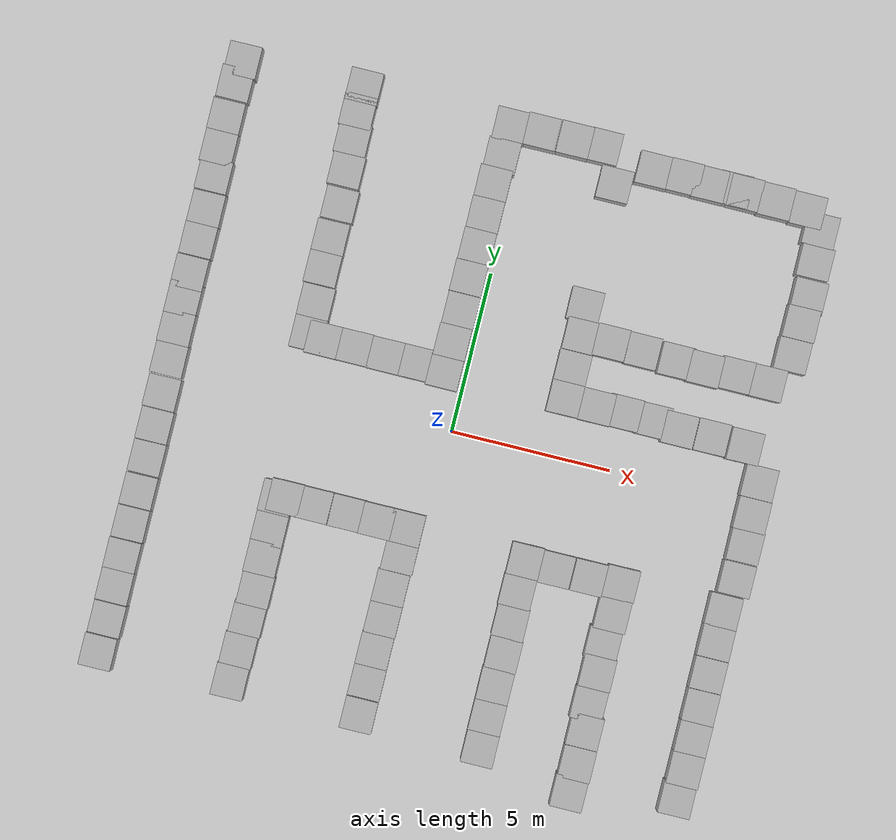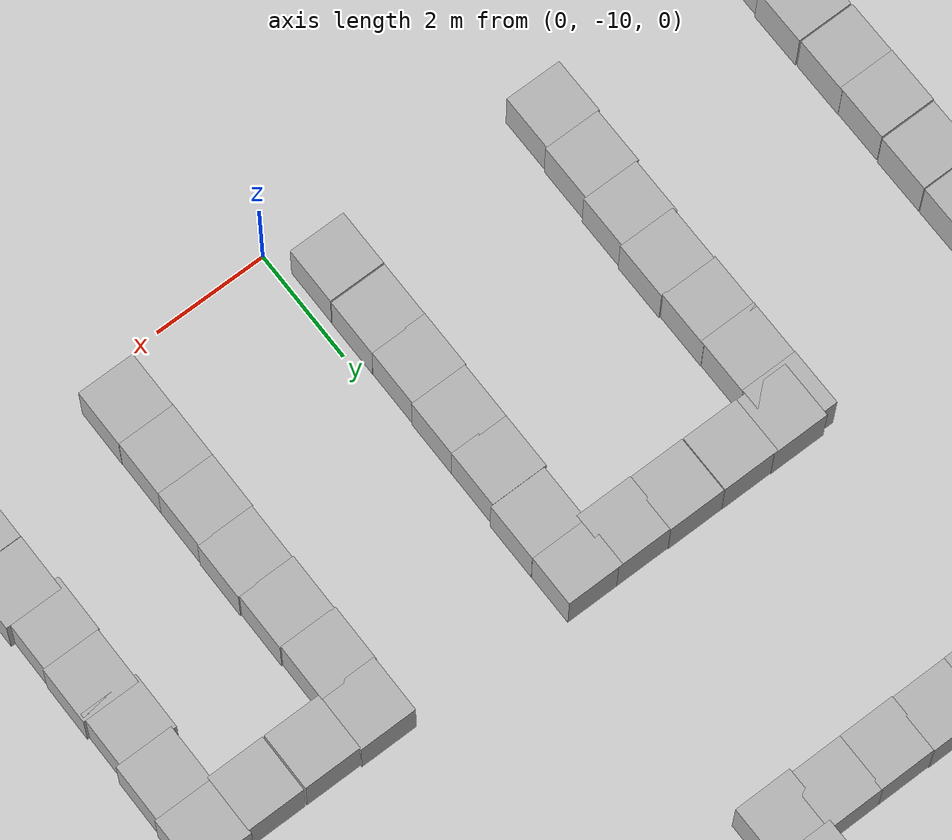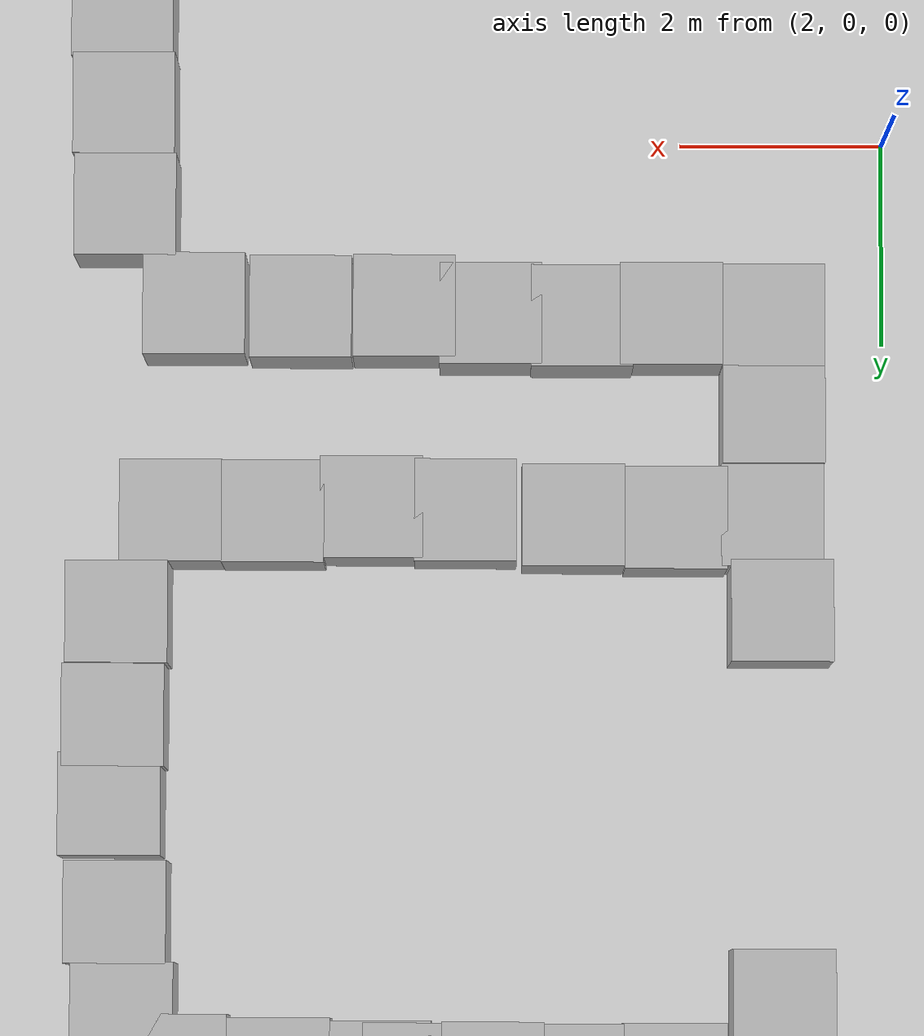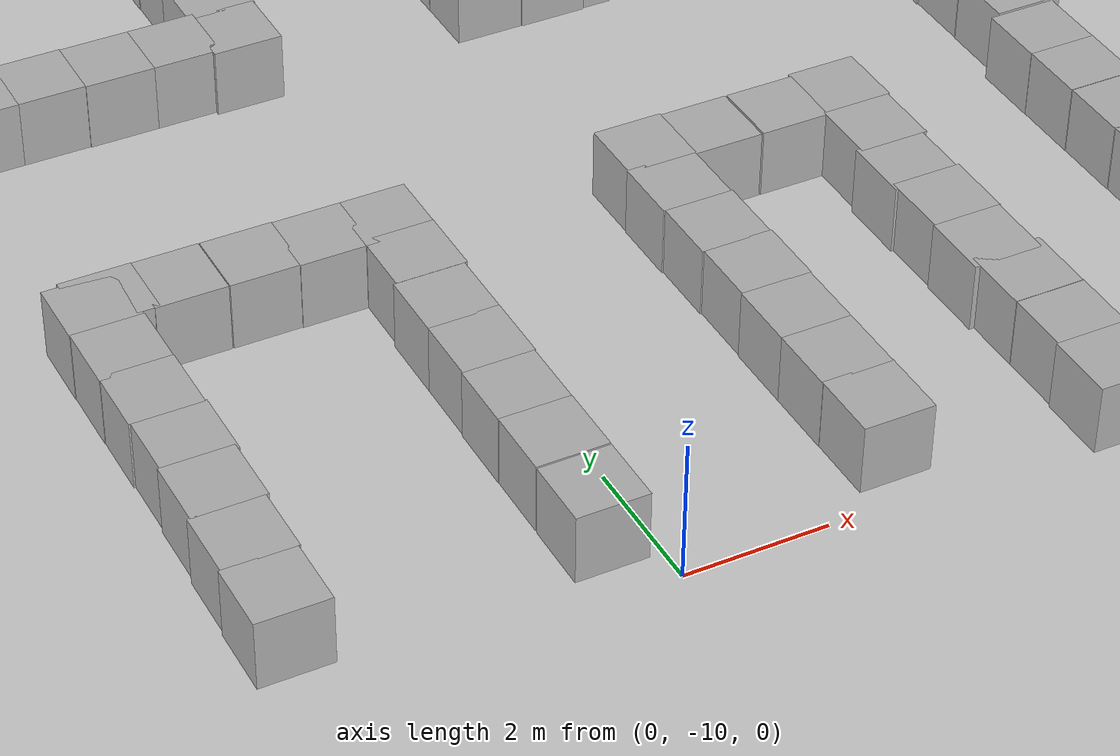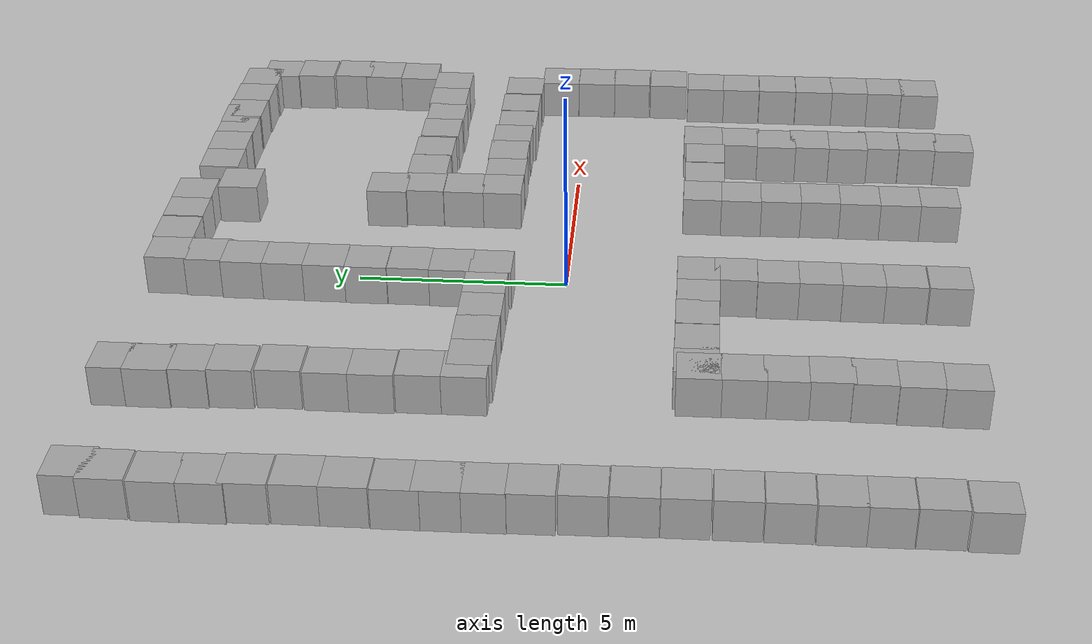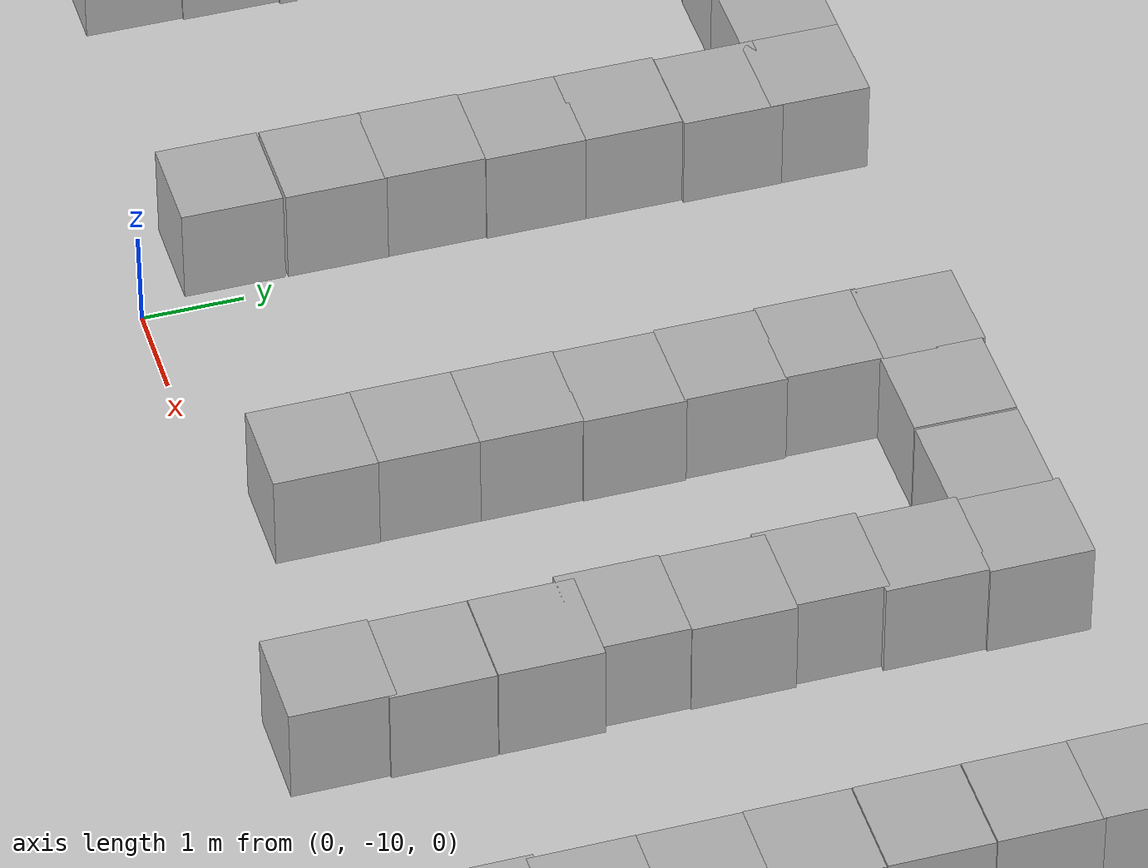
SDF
<sdf version='1.9'>
  <world name='empty'>
    <physics name='1ms' type='ignored'>
      <max_step_size>0.001</max_step_size>
      <real_time_factor>1</real_time_factor>
      <real_time_update_rate>1000</real_time_update_rate>
    </physics>
    <plugin filename="libignition-gazebo-sensors-system.so"
        name="ignition::gazebo::systems::Sensors">
  <render_engine>ogre2</render_engine>
</plugin>
    <plugin name='gz::sim::systems::Physics' filename='ignition-gazebo-physics-system'/>
    <plugin name='gz::sim::systems::UserCommands' filename='ignition-gazebo-user-commands-system'/>
    <plugin name='gz::sim::systems::SceneBroadcaster' filename='ignition-gazebo-scene-broadcaster-system'/>
    <plugin name='gz::sim::systems::Contact' filename='ignition-gazebo-contact-system'/>
    <gravity>0 0 -9.8</gravity>
    <magnetic_field>6e-06 2.3e-05 -4.2e-05</magnetic_field>
    <atmosphere type='adiabatic'/>
    <scene>
      <ambient>0.4 0.4 0.4 1</ambient>
      <background>0.7 0.7 0.7 1</background>
      <shadows>true</shadows>
    </scene>
    <model name='ground_plane'>
      <static>true</static>
      <link name='link'>
        <collision name='collision'>
          <geometry>
            <plane>
              <normal>0 0 1</normal>
              <size>100 100</size>
            </plane>
          </geometry>
          <surface>
            <friction>
              <ode/>
            </friction>
            <bounce/>
            <contact/>
          </surface>
        </collision>
        <visual name='visual'>
          <geometry>
            <plane>
              <normal>0 0 1</normal>
              <size>100 100</size>
            </plane>
          </geometry>
          <material>
            <ambient>0.8 0.8 0.8 1</ambient>
            <diffuse>0.8 0.8 0.8 1</diffuse>
            <specular>0.8 0.8 0.8 1</specular>
          </material>
        </visual>
        <pose>0 0 0 0 -0 0</pose>
        <inertial>
          <pose>0 0 0 0 -0 0</pose>
          <mass>1</mass>
          <inertia>
            <ixx>1</ixx>
            <ixy>0</ixy>
            <ixz>0</ixz>
            <iyy>1</iyy>
            <iyz>0</iyz>
            <izz>1</izz>
          </inertia>
        </inertial>
        <enable_wind>false</enable_wind>
      </link>
      <pose>0 0 0 0 -0 0</pose>
      <self_collide>false</self_collide>
    </model>
    <model name='box'>
      <pose>-0.628622 -3.17576 0.5 0 -0 0</pose>
      <link name='box_link'>
        <inertial>
          <inertia>
            <ixx>0.16666</ixx>
            <ixy>0</ixy>
            <ixz>0</ixz>
            <iyy>0.16666</iyy>
            <iyz>0</iyz>
            <izz>0.16666</izz>
          </inertia>
          <mass>1</mass>
          <pose>0 0 0 0 -0 0</pose>
        </inertial>
        <collision name='box_collision'>
          <geometry>
            <box>
              <size>1 1 1</size>
            </box>
          </geometry>
          <surface>
            <friction>
              <ode/>
            </friction>
            <bounce/>
            <contact/>
          </surface>
        </collision>
        <visual name='box_visual'>
          <geometry>
            <box>
              <size>1 1 1</size>
            </box>
          </geometry>
          <material>
            <ambient>0.3 0.3 0.3 1</ambient>
            <diffuse>0.7 0.7 0.7 1</diffuse>
            <specular>1 1 1 1</specular>
          </material>
        </visual>
        <pose>0 0 0 0 -0 0</pose>
        <enable_wind>false</enable_wind>
      </link>
      <static>false</static>
      <self_collide>false</self_collide>
    </model>
    <model name='box_0'>
      <pose>-1.54573 -3.17539 0.5 0 -0 0</pose>
      <link name='box_link'>
        <inertial>
          <inertia>
            <ixx>0.16666</ixx>
            <ixy>0</ixy>
            <ixz>0</ixz>
            <iyy>0.16666</iyy>
            <iyz>0</iyz>
            <izz>0.16666</izz>
          </inertia>
          <mass>1</mass>
          <pose>0 0 0 0 -0 0</pose>
        </inertial>
        <collision name='box_collision'>
          <geometry>
            <box>
              <size>1 1 1</size>
            </box>
          </geometry>
          <surface>
            <friction>
              <ode/>
            </friction>
            <bounce/>
            <contact/>
          </surface>
        </collision>
        <visual name='box_visual'>
          <geometry>
            <box>
              <size>1 1 1</size>
            </box>
          </geometry>
          <material>
            <ambient>0.3 0.3 0.3 1</ambient>
            <diffuse>0.7 0.7 0.7 1</diffuse>
            <specular>1 1 1 1</specular>
          </material>
        </visual>
        <pose>0 0 0 0 -0 0</pose>
        <enable_wind>false</enable_wind>
      </link>
      <static>false</static>
      <self_collide>false</self_collide>
    </model>
    <model name='box_1'>
      <pose>-2.50675 -3.16277 0.5 0 -0 0</pose>
      <link name='box_link'>
        <inertial>
          <inertia>
            <ixx>0.16666</ixx>
            <ixy>0</ixy>
            <ixz>0</ixz>
            <iyy>0.16666</iyy>
            <iyz>0</iyz>
            <izz>0.16666</izz>
          </inertia>
          <mass>1</mass>
          <pose>0 0 0 0 -0 0</pose>
        </inertial>
        <collision name='box_collision'>
          <geometry>
            <box>
              <size>1 1 1</size>
            </box>
          </geometry>
          <surface>
            <friction>
              <ode/>
            </friction>
            <bounce/>
            <contact/>
          </surface>
        </collision>
        <visual name='box_visual'>
          <geometry>
            <box>
              <size>1 1 1</size>
            </box>
          </geometry>
          <material>
            <ambient>0.3 0.3 0.3 1</ambient>
            <diffuse>0.7 0.7 0.7 1</diffuse>
            <specular>1 1 1 1</specular>
          </material>
        </visual>
        <pose>0 0 0 0 -0 0</pose>
        <enable_wind>false</enable_wind>
      </link>
      <static>false</static>
      <self_collide>false</self_collide>
    </model>
    <model name='box_2'>
      <pose>-3.51964 -3.15896 0.5 0 -0 0</pose>
      <link name='box_link'>
        <inertial>
          <inertia>
            <ixx>0.16666</ixx>
            <ixy>0</ixy>
            <ixz>0</ixz>
            <iyy>0.16666</iyy>
            <iyz>0</iyz>
            <izz>0.16666</izz>
          </inertia>
          <mass>1</mass>
          <pose>0 0 0 0 -0 0</pose>
        </inertial>
        <collision name='box_collision'>
          <geometry>
            <box>
              <size>1 1 1</size>
            </box>
          </geometry>
          <surface>
            <friction>
              <ode/>
            </friction>
            <bounce/>
            <contact/>
          </surface>
        </collision>
        <visual name='box_visual'>
          <geometry>
            <box>
              <size>1 1 1</size>
            </box>
          </geometry>
          <material>
            <ambient>0.3 0.3 0.3 1</ambient>
            <diffuse>0.7 0.7 0.7 1</diffuse>
            <specular>1 1 1 1</specular>
          </material>
        </visual>
        <pose>0 0 0 0 -0 0</pose>
        <enable_wind>false</enable_wind>
      </link>
      <static>false</static>
      <self_collide>false</self_collide>
    </model>
    <model name='box_3'>
      <pose>-4.44088 -3.14907 0.5 0 -0 0</pose>
      <link name='box_link'>
        <inertial>
          <inertia>
            <ixx>0.16666</ixx>
            <ixy>0</ixy>
            <ixz>0</ixz>
            <iyy>0.16666</iyy>
            <iyz>0</iyz>
            <izz>0.16666</izz>
          </inertia>
          <mass>1</mass>
          <pose>0 0 0 0 -0 0</pose>
        </inertial>
        <collision name='box_collision'>
          <geometry>
            <box>
              <size>1 1 1</size>
            </box>
          </geometry>
          <surface>
            <friction>
              <ode/>
            </friction>
            <bounce/>
            <contact/>
          </surface>
        </collision>
        <visual name='box_visual'>
          <geometry>
            <box>
              <size>1 1 1</size>
            </box>
          </geometry>
          <material>
            <ambient>0.3 0.3 0.3 1</ambient>
            <diffuse>0.7 0.7 0.7 1</diffuse>
            <specular>1 1 1 1</specular>
          </material>
        </visual>
        <pose>0 0 0 0 -0 0</pose>
        <enable_wind>false</enable_wind>
      </link>
      <static>false</static>
      <self_collide>false</self_collide>
    </model>
    <model name='box_3_1'>
      <pose>-4.46258 1.78849 0.5 0 -0 0</pose>
      <link name='box_link'>
        <inertial>
          <inertia>
            <ixx>0.16666</ixx>
            <ixy>0</ixy>
            <ixz>0</ixz>
            <iyy>0.16666</iyy>
            <iyz>0</iyz>
            <izz>0.16666</izz>
          </inertia>
          <mass>1</mass>
        </inertial>
        <collision name='box_collision'>
          <geometry>
            <box>
              <size>1 1 1</size>
            </box>
          </geometry>
          <surface>
            <friction>
              <ode/>
            </friction>
            <bounce/>
            <contact/>
          </surface>
        </collision>
        <visual name='box_visual'>
          <geometry>
            <box>
              <size>1 1 1</size>
            </box>
          </geometry>
          <material>
            <ambient>0.3 0.3 0.3 1</ambient>
            <diffuse>0.7 0.7 0.7 1</diffuse>
            <specular>1 1 1 1</specular>
          </material>
        </visual>
      </link>
      <static>false</static>
      <self_collide>false</self_collide>
    </model>
    <model name='box_4'>
      <pose>-3.47193 1.7902 0.5 0 -0 0</pose>
      <link name='box_link'>
        <inertial>
          <inertia>
            <ixx>0.16666</ixx>
            <ixy>0</ixy>
            <ixz>0</ixz>
            <iyy>0.16666</iyy>
            <iyz>0</iyz>
            <izz>0.16666</izz>
          </inertia>
          <mass>1</mass>
          <pose>0 0 0 0 -0 0</pose>
        </inertial>
        <collision name='box_collision'>
          <geometry>
            <box>
              <size>1 1 1</size>
            </box>
          </geometry>
          <surface>
            <friction>
              <ode/>
            </friction>
            <bounce/>
            <contact/>
          </surface>
        </collision>
        <visual name='box_visual'>
          <geometry>
            <box>
              <size>1 1 1</size>
            </box>
          </geometry>
          <material>
            <ambient>0.3 0.3 0.3 1</ambient>
            <diffuse>0.7 0.7 0.7 1</diffuse>
            <specular>1 1 1 1</specular>
          </material>
        </visual>
        <pose>0 0 0 0 -0 0</pose>
        <enable_wind>false</enable_wind>
      </link>
      <static>false</static>
      <self_collide>false</self_collide>
    </model>
    <model name='box_5'>
      <pose>-2.5012 1.77664 0.5 0 -0 0</pose>
      <link name='box_link'>
        <inertial>
          <inertia>
            <ixx>0.16666</ixx>
            <ixy>0</ixy>
            <ixz>0</ixz>
            <iyy>0.16666</iyy>
            <iyz>0</iyz>
            <izz>0.16666</izz>
          </inertia>
          <mass>1</mass>
          <pose>0 0 0 0 -0 0</pose>
        </inertial>
        <collision name='box_collision'>
          <geometry>
            <box>
              <size>1 1 1</size>
            </box>
          </geometry>
          <surface>
            <friction>
              <ode/>
            </friction>
            <bounce/>
            <contact/>
          </surface>
        </collision>
        <visual name='box_visual'>
          <geometry>
            <box>
              <size>1 1 1</size>
            </box>
          </geometry>
          <material>
            <ambient>0.3 0.3 0.3 1</ambient>
            <diffuse>0.7 0.7 0.7 1</diffuse>
            <specular>1 1 1 1</specular>
          </material>
        </visual>
        <pose>0 0 0 0 -0 0</pose>
        <enable_wind>false</enable_wind>
      </link>
      <static>false</static>
      <self_collide>false</self_collide>
    </model>
    <model name='box_6'>
      <pose>-1.52755 1.77711 0.5 0 -0 0</pose>
      <link name='box_link'>
        <inertial>
          <inertia>
            <ixx>0.16666</ixx>
            <ixy>0</ixy>
            <ixz>0</ixz>
            <iyy>0.16666</iyy>
            <iyz>0</iyz>
            <izz>0.16666</izz>
          </inertia>
          <mass>1</mass>
          <pose>0 0 0 0 -0 0</pose>
        </inertial>
        <collision name='box_collision'>
          <geometry>
            <box>
              <size>1 1 1</size>
            </box>
          </geometry>
          <surface>
            <friction>
              <ode/>
            </friction>
            <bounce/>
            <contact/>
          </surface>
        </collision>
        <visual name='box_visual'>
          <geometry>
            <box>
              <size>1 1 1</size>
            </box>
          </geometry>
          <material>
            <ambient>0.3 0.3 0.3 1</ambient>
            <diffuse>0.7 0.7 0.7 1</diffuse>
            <specular>1 1 1 1</specular>
          </material>
        </visual>
        <pose>0 0 0 0 -0 0</pose>
        <enable_wind>false</enable_wind>
      </link>
      <static>false</static>
      <self_collide>false</self_collide>
    </model>
    <model name='box_7'>
      <pose>-0.640154 1.71751 0.5 0 -0 0</pose>
      <link name='box_link'>
        <inertial>
          <inertia>
            <ixx>0.16666</ixx>
            <ixy>0</ixy>
            <ixz>0</ixz>
            <iyy>0.16666</iyy>
            <iyz>0</iyz>
            <izz>0.16666</izz>
          </inertia>
          <mass>1</mass>
          <pose>0 0 0 0 -0 0</pose>
        </inertial>
        <collision name='box_collision'>
          <geometry>
            <box>
              <size>1 1 1</size>
            </box>
          </geometry>
          <surface>
            <friction>
              <ode/>
            </friction>
            <bounce/>
            <contact/>
          </surface>
        </collision>
        <visual name='box_visual'>
          <geometry>
            <box>
              <size>1 1 1</size>
            </box>
          </geometry>
          <material>
            <ambient>0.3 0.3 0.3 1</ambient>
            <diffuse>0.7 0.7 0.7 1</diffuse>
            <specular>1 1 1 1</specular>
          </material>
        </visual>
        <pose>0 0 0 0 -0 0</pose>
        <enable_wind>false</enable_wind>
      </link>
      <static>false</static>
      <self_collide>false</self_collide>
    </model>
    <model name='box_8'>
      <pose>-0.624925 -4.05306 0.5 0 -0 0</pose>
      <link name='box_link'>
        <inertial>
          <inertia>
            <ixx>0.16666</ixx>
            <ixy>0</ixy>
            <ixz>0</ixz>
            <iyy>0.16666</iyy>
            <iyz>0</iyz>
            <izz>0.16666</izz>
          </inertia>
          <mass>1</mass>
          <pose>0 0 0 0 -0 0</pose>
        </inertial>
        <collision name='box_collision'>
          <geometry>
            <box>
              <size>1 1 1</size>
            </box>
          </geometry>
          <surface>
            <friction>
              <ode/>
            </friction>
            <bounce/>
            <contact/>
          </surface>
        </collision>
        <visual name='box_visual'>
          <geometry>
            <box>
              <size>1 1 1</size>
            </box>
          </geometry>
          <material>
            <ambient>0.3 0.3 0.3 1</ambient>
            <diffuse>0.7 0.7 0.7 1</diffuse>
            <specular>1 1 1 1</specular>
          </material>
        </visual>
        <pose>0 0 0 0 -0 0</pose>
        <enable_wind>false</enable_wind>
      </link>
      <static>false</static>
      <self_collide>false</self_collide>
    </model>
    <model name='box_9'>
      <pose>-0.666125 -5.05588 0.5 0 -0 0</pose>
      <link name='box_link'>
        <inertial>
          <inertia>
            <ixx>0.16666</ixx>
            <ixy>0</ixy>
            <ixz>0</ixz>
            <iyy>0.16666</iyy>
            <iyz>0</iyz>
            <izz>0.16666</izz>
          </inertia>
          <mass>1</mass>
          <pose>0 0 0 0 -0 0</pose>
        </inertial>
        <collision name='box_collision'>
          <geometry>
            <box>
              <size>1 1 1</size>
            </box>
          </geometry>
          <surface>
            <friction>
              <ode/>
            </friction>
            <bounce/>
            <contact/>
          </surface>
        </collision>
        <visual name='box_visual'>
          <geometry>
            <box>
              <size>1 1 1</size>
            </box>
          </geometry>
          <material>
            <ambient>0.3 0.3 0.3 1</ambient>
            <diffuse>0.7 0.7 0.7 1</diffuse>
            <specular>1 1 1 1</specular>
          </material>
        </visual>
        <pose>0 0 0 0 -0 0</pose>
        <enable_wind>false</enable_wind>
      </link>
      <static>false</static>
      <self_collide>false</self_collide>
    </model>
    <model name='box_10'>
      <pose>-0.666125 -6.02587 0.5 0 -0 0</pose>
      <link name='box_link'>
        <inertial>
          <inertia>
            <ixx>0.16666</ixx>
            <ixy>0</ixy>
            <ixz>0</ixz>
            <iyy>0.16666</iyy>
            <iyz>0</iyz>
            <izz>0.16666</izz>
          </inertia>
          <mass>1</mass>
          <pose>0 0 0 0 -0 0</pose>
        </inertial>
        <collision name='box_collision'>
          <geometry>
            <box>
              <size>1 1 1</size>
            </box>
          </geometry>
          <surface>
            <friction>
              <ode/>
            </friction>
            <bounce/>
            <contact/>
          </surface>
        </collision>
        <visual name='box_visual'>
          <geometry>
            <box>
              <size>1 1 1</size>
            </box>
          </geometry>
          <material>
            <ambient>0.3 0.3 0.3 1</ambient>
            <diffuse>0.7 0.7 0.7 1</diffuse>
            <specular>1 1 1 1</specular>
          </material>
        </visual>
        <pose>0 0 0 0 -0 0</pose>
        <enable_wind>false</enable_wind>
      </link>
      <static>false</static>
      <self_collide>false</self_collide>
    </model>
    <model name='box_11'>
      <pose>-0.682233 -7.0253 0.5 0 -0 0</pose>
      <link name='box_link'>
        <inertial>
          <inertia>
            <ixx>0.16666</ixx>
            <ixy>0</ixy>
            <ixz>0</ixz>
            <iyy>0.16666</iyy>
            <iyz>0</iyz>
            <izz>0.16666</izz>
          </inertia>
          <mass>1</mass>
          <pose>0 0 0 0 -0 0</pose>
        </inertial>
        <collision name='box_collision'>
          <geometry>
            <box>
              <size>1 1 1</size>
            </box>
          </geometry>
          <surface>
            <friction>
              <ode/>
            </friction>
            <bounce/>
            <contact/>
          </surface>
        </collision>
        <visual name='box_visual'>
          <geometry>
            <box>
              <size>1 1 1</size>
            </box>
          </geometry>
          <material>
            <ambient>0.3 0.3 0.3 1</ambient>
            <diffuse>0.7 0.7 0.7 1</diffuse>
            <specular>1 1 1 1</specular>
          </material>
        </visual>
        <pose>0 0 0 0 -0 0</pose>
        <enable_wind>false</enable_wind>
      </link>
      <static>false</static>
      <self_collide>false</self_collide>
    </model>
    <model name='box_12'>
      <pose>-0.678292 -8.00642 0.500001 0 -0 0</pose>
      <link name='box_link'>
        <inertial>
          <inertia>
            <ixx>0.16666</ixx>
            <ixy>0</ixy>
            <ixz>0</ixz>
            <iyy>0.16666</iyy>
            <iyz>0</iyz>
            <izz>0.16666</izz>
          </inertia>
          <mass>1</mass>
          <pose>0 0 0 0 -0 0</pose>
        </inertial>
        <collision name='box_collision'>
          <geometry>
            <box>
              <size>1 1 1</size>
            </box>
          </geometry>
          <surface>
            <friction>
              <ode/>
            </friction>
            <bounce/>
            <contact/>
          </surface>
        </collision>
        <visual name='box_visual'>
          <geometry>
            <box>
              <size>1 1 1</size>
            </box>
          </geometry>
          <material>
            <ambient>0.3 0.3 0.3 1</ambient>
            <diffuse>0.7 0.7 0.7 1</diffuse>
            <specular>1 1 1 1</specular>
          </material>
        </visual>
        <pose>0 0 0 0 -0 0</pose>
        <enable_wind>false</enable_wind>
      </link>
      <static>false</static>
      <self_collide>false</self_collide>
    </model>
    <model name='box_13'>
      <pose>-0.682523 -9.03062 0.5 0 -0 0</pose>
      <link name='box_link'>
        <inertial>
          <inertia>
            <ixx>0.16666</ixx>
            <ixy>0</ixy>
            <ixz>0</ixz>
            <iyy>0.16666</iyy>
            <iyz>0</iyz>
            <izz>0.16666</izz>
          </inertia>
          <mass>1</mass>
          <pose>0 0 0 0 -0 0</pose>
        </inertial>
        <collision name='box_collision'>
          <geometry>
            <box>
              <size>1 1 1</size>
            </box>
          </geometry>
          <surface>
            <friction>
              <ode/>
            </friction>
            <bounce/>
            <contact/>
          </surface>
        </collision>
        <visual name='box_visual'>
          <geometry>
            <box>
              <size>1 1 1</size>
            </box>
          </geometry>
          <material>
            <ambient>0.3 0.3 0.3 1</ambient>
            <diffuse>0.7 0.7 0.7 1</diffuse>
            <specular>1 1 1 1</specular>
          </material>
        </visual>
        <pose>0 0 0 0 -0 0</pose>
        <enable_wind>false</enable_wind>
      </link>
      <static>false</static>
      <self_collide>false</self_collide>
    </model>
    <model name='box_14'>
      <pose>-0.62645 2.66518 0.5 0 -0 0</pose>
      <link name='box_link'>
        <inertial>
          <inertia>
            <ixx>0.16666</ixx>
            <ixy>0</ixy>
            <ixz>0</ixz>
            <iyy>0.16666</iyy>
            <iyz>0</iyz>
            <izz>0.16666</izz>
          </inertia>
          <mass>1</mass>
          <pose>0 0 0 0 -0 0</pose>
        </inertial>
        <collision name='box_collision'>
          <geometry>
            <box>
              <size>1 1 1</size>
            </box>
          </geometry>
          <surface>
            <friction>
              <ode/>
            </friction>
            <bounce/>
            <contact/>
          </surface>
        </collision>
        <visual name='box_visual'>
          <geometry>
            <box>
              <size>1 1 1</size>
            </box>
          </geometry>
          <material>
            <ambient>0.3 0.3 0.3 1</ambient>
            <diffuse>0.7 0.7 0.7 1</diffuse>
            <specular>1 1 1 1</specular>
          </material>
        </visual>
        <pose>0 0 0 0 -0 0</pose>
        <enable_wind>false</enable_wind>
      </link>
      <static>false</static>
      <self_collide>false</self_collide>
    </model>
    <model name='box_15'>
      <pose>-0.602355 3.6627 0.5 0 -0 0</pose>
      <link name='box_link'>
        <inertial>
          <inertia>
            <ixx>0.16666</ixx>
            <ixy>0</ixy>
            <ixz>0</ixz>
            <iyy>0.16666</iyy>
            <iyz>0</iyz>
            <izz>0.16666</izz>
          </inertia>
          <mass>1</mass>
          <pose>0 0 0 0 -0 0</pose>
        </inertial>
        <collision name='box_collision'>
          <geometry>
            <box>
              <size>1 1 1</size>
            </box>
          </geometry>
          <surface>
            <friction>
              <ode/>
            </friction>
            <bounce/>
            <contact/>
          </surface>
        </collision>
        <visual name='box_visual'>
          <geometry>
            <box>
              <size>1 1 1</size>
            </box>
          </geometry>
          <material>
            <ambient>0.3 0.3 0.3 1</ambient>
            <diffuse>0.7 0.7 0.7 1</diffuse>
            <specular>1 1 1 1</specular>
          </material>
        </visual>
        <pose>0 0 0 0 -0 0</pose>
        <enable_wind>false</enable_wind>
      </link>
      <static>false</static>
      <self_collide>false</self_collide>
    </model>
    <model name='box_16'>
      <pose>-0.610927 4.67319 0.5 0 -0 0</pose>
      <link name='box_link'>
        <inertial>
          <inertia>
            <ixx>0.16666</ixx>
            <ixy>0</ixy>
            <ixz>0</ixz>
            <iyy>0.16666</iyy>
            <iyz>0</iyz>
            <izz>0.16666</izz>
          </inertia>
          <mass>1</mass>
          <pose>0 0 0 0 -0 0</pose>
        </inertial>
        <collision name='box_collision'>
          <geometry>
            <box>
              <size>1 1 1</size>
            </box>
          </geometry>
          <surface>
            <friction>
              <ode/>
            </friction>
            <bounce/>
            <contact/>
          </surface>
        </collision>
        <visual name='box_visual'>
          <geometry>
            <box>
              <size>1 1 1</size>
            </box>
          </geometry>
          <material>
            <ambient>0.3 0.3 0.3 1</ambient>
            <diffuse>0.7 0.7 0.7 1</diffuse>
            <specular>1 1 1 1</specular>
          </material>
        </visual>
        <pose>0 0 0 0 -0 0</pose>
        <enable_wind>false</enable_wind>
      </link>
      <static>false</static>
      <self_collide>false</self_collide>
    </model>
    <model name='box_17'>
      <pose>-0.595787 5.67413 0.5 0 -0 0</pose>
      <link name='box_link'>
        <inertial>
          <inertia>
            <ixx>0.16666</ixx>
            <ixy>0</ixy>
            <ixz>0</ixz>
            <iyy>0.16666</iyy>
            <iyz>0</iyz>
            <izz>0.16666</izz>
          </inertia>
          <mass>1</mass>
          <pose>0 0 0 0 -0 0</pose>
        </inertial>
        <collision name='box_collision'>
          <geometry>
            <box>
              <size>1 1 1</size>
            </box>
          </geometry>
          <surface>
            <friction>
              <ode/>
            </friction>
            <bounce/>
            <contact/>
          </surface>
        </collision>
        <visual name='box_visual'>
          <geometry>
            <box>
              <size>1 1 1</size>
            </box>
          </geometry>
          <material>
            <ambient>0.3 0.3 0.3 1</ambient>
            <diffuse>0.7 0.7 0.7 1</diffuse>
            <specular>1 1 1 1</specular>
          </material>
        </visual>
        <pose>0 0 0 0 -0 0</pose>
        <enable_wind>false</enable_wind>
      </link>
      <static>false</static>
      <self_collide>false</self_collide>
    </model>
    <model name='box_18'>
      <pose>-0.583933 6.66382 0.5 0 -0 0</pose>
      <link name='box_link'>
        <inertial>
          <inertia>
            <ixx>0.16666</ixx>
            <ixy>0</ixy>
            <ixz>0</ixz>
            <iyy>0.16666</iyy>
            <iyz>0</iyz>
            <izz>0.16666</izz>
          </inertia>
          <mass>1</mass>
          <pose>0 0 0 0 -0 0</pose>
        </inertial>
        <collision name='box_collision'>
          <geometry>
            <box>
              <size>1 1 1</size>
            </box>
          </geometry>
          <surface>
            <friction>
              <ode/>
            </friction>
            <bounce/>
            <contact/>
          </surface>
        </collision>
        <visual name='box_visual'>
          <geometry>
            <box>
              <size>1 1 1</size>
            </box>
          </geometry>
          <material>
            <ambient>0.3 0.3 0.3 1</ambient>
            <diffuse>0.7 0.7 0.7 1</diffuse>
            <specular>1 1 1 1</specular>
          </material>
        </visual>
        <pose>0 0 0 0 -0 0</pose>
        <enable_wind>false</enable_wind>
      </link>
      <static>false</static>
      <self_collide>false</self_collide>
    </model>
    <model name='box_19'>
      <pose>-0.575678 7.6423 0.5 0 -0 0</pose>
      <link name='box_link'>
        <inertial>
          <inertia>
            <ixx>0.16666</ixx>
            <ixy>0</ixy>
            <ixz>0</ixz>
            <iyy>0.16666</iyy>
            <iyz>0</iyz>
            <izz>0.16666</izz>
          </inertia>
          <mass>1</mass>
          <pose>0 0 0 0 -0 0</pose>
        </inertial>
        <collision name='box_collision'>
          <geometry>
            <box>
              <size>1 1 1</size>
            </box>
          </geometry>
          <surface>
            <friction>
              <ode/>
            </friction>
            <bounce/>
            <contact/>
          </surface>
        </collision>
        <visual name='box_visual'>
          <geometry>
            <box>
              <size>1 1 1</size>
            </box>
          </geometry>
          <material>
            <ambient>0.3 0.3 0.3 1</ambient>
            <diffuse>0.7 0.7 0.7 1</diffuse>
            <specular>1 1 1 1</specular>
          </material>
        </visual>
        <pose>0 0 0 0 -0 0</pose>
        <enable_wind>false</enable_wind>
      </link>
      <static>false</static>
      <self_collide>false</self_collide>
    </model>
    <model name='box_20'>
      <pose>3.11918 -3.27527 0.5 0 -0 0</pose>
      <link name='box_link'>
        <inertial>
          <inertia>
            <ixx>0.16666</ixx>
            <ixy>0</ixy>
            <ixz>0</ixz>
            <iyy>0.16666</iyy>
            <iyz>0</iyz>
            <izz>0.16666</izz>
          </inertia>
          <mass>1</mass>
          <pose>0 0 0 0 -0 0</pose>
        </inertial>
        <collision name='box_collision'>
          <geometry>
            <box>
              <size>1 1 1</size>
            </box>
          </geometry>
          <surface>
            <friction>
              <ode/>
            </friction>
            <bounce/>
            <contact/>
          </surface>
        </collision>
        <visual name='box_visual'>
          <geometry>
            <box>
              <size>1 1 1</size>
            </box>
          </geometry>
          <material>
            <ambient>0.3 0.3 0.3 1</ambient>
            <diffuse>0.7 0.7 0.7 1</diffuse>
            <specular>1 1 1 1</specular>
          </material>
        </visual>
        <pose>0 0 0 0 -0 0</pose>
        <enable_wind>false</enable_wind>
      </link>
      <static>false</static>
      <self_collide>false</self_collide>
    </model>
    <model name='box_21'>
      <pose>3.10814 -4.22657 0.5 0 -0 0</pose>
      <link name='box_link'>
        <inertial>
          <inertia>
            <ixx>0.16666</ixx>
            <ixy>0</ixy>
            <ixz>0</ixz>
            <iyy>0.16666</iyy>
            <iyz>0</iyz>
            <izz>0.16666</izz>
          </inertia>
          <mass>1</mass>
          <pose>0 0 0 0 -0 0</pose>
        </inertial>
        <collision name='box_collision'>
          <geometry>
            <box>
              <size>1 1 1</size>
            </box>
          </geometry>
          <surface>
            <friction>
              <ode/>
            </friction>
            <bounce/>
            <contact/>
          </surface>
        </collision>
        <visual name='box_visual'>
          <geometry>
            <box>
              <size>1 1 1</size>
            </box>
          </geometry>
          <material>
            <ambient>0.3 0.3 0.3 1</ambient>
            <diffuse>0.7 0.7 0.7 1</diffuse>
            <specular>1 1 1 1</specular>
          </material>
        </visual>
        <pose>0 0 0 0 -0 0</pose>
        <enable_wind>false</enable_wind>
      </link>
      <static>false</static>
      <self_collide>false</self_collide>
    </model>
    <model name='box_22'>
      <pose>3.12982 -5.21504 0.5 0 -0 0</pose>
      <link name='box_link'>
        <inertial>
          <inertia>
            <ixx>0.16666</ixx>
            <ixy>0</ixy>
            <ixz>0</ixz>
            <iyy>0.16666</iyy>
            <iyz>0</iyz>
            <izz>0.16666</izz>
          </inertia>
          <mass>1</mass>
          <pose>0 0 0 0 -0 0</pose>
        </inertial>
        <collision name='box_collision'>
          <geometry>
            <box>
              <size>1 1 1</size>
            </box>
          </geometry>
          <surface>
            <friction>
              <ode/>
            </friction>
            <bounce/>
            <contact/>
          </surface>
        </collision>
        <visual name='box_visual'>
          <geometry>
            <box>
              <size>1 1 1</size>
            </box>
          </geometry>
          <material>
            <ambient>0.3 0.3 0.3 1</ambient>
            <diffuse>0.7 0.7 0.7 1</diffuse>
            <specular>1 1 1 1</specular>
          </material>
        </visual>
        <pose>0 0 0 0 -0 0</pose>
        <enable_wind>false</enable_wind>
      </link>
      <static>false</static>
      <self_collide>false</self_collide>
    </model>
    <model name='box_23'>
      <pose>3.15098 -6.19862 0.5 0 -0 0</pose>
      <link name='box_link'>
        <inertial>
          <inertia>
            <ixx>0.16666</ixx>
            <ixy>0</ixy>
            <ixz>0</ixz>
            <iyy>0.16666</iyy>
            <iyz>0</iyz>
            <izz>0.16666</izz>
          </inertia>
          <mass>1</mass>
          <pose>0 0 0 0 -0 0</pose>
        </inertial>
        <collision name='box_collision'>
          <geometry>
            <box>
              <size>1 1 1</size>
            </box>
          </geometry>
          <surface>
            <friction>
              <ode/>
            </friction>
            <bounce/>
            <contact/>
          </surface>
        </collision>
        <visual name='box_visual'>
          <geometry>
            <box>
              <size>1 1 1</size>
            </box>
          </geometry>
          <material>
            <ambient>0.3 0.3 0.3 1</ambient>
            <diffuse>0.7 0.7 0.7 1</diffuse>
            <specular>1 1 1 1</specular>
          </material>
        </visual>
        <pose>0 0 0 0 -0 0</pose>
        <enable_wind>false</enable_wind>
      </link>
      <static>false</static>
      <self_collide>false</self_collide>
    </model>
    <model name='box_24'>
      <pose>3.13753 -7.18844 0.5 0 -0 0</pose>
      <link name='box_link'>
        <inertial>
          <inertia>
            <ixx>0.16666</ixx>
            <ixy>0</ixy>
            <ixz>0</ixz>
            <iyy>0.16666</iyy>
            <iyz>0</iyz>
            <izz>0.16666</izz>
          </inertia>
          <mass>1</mass>
          <pose>0 0 0 0 -0 0</pose>
        </inertial>
        <collision name='box_collision'>
          <geometry>
            <box>
              <size>1 1 1</size>
            </box>
          </geometry>
          <surface>
            <friction>
              <ode/>
            </friction>
            <bounce/>
            <contact/>
          </surface>
        </collision>
        <visual name='box_visual'>
          <geometry>
            <box>
              <size>1 1 1</size>
            </box>
          </geometry>
          <material>
            <ambient>0.3 0.3 0.3 1</ambient>
            <diffuse>0.7 0.7 0.7 1</diffuse>
            <specular>1 1 1 1</specular>
          </material>
        </visual>
        <pose>0 0 0 0 -0 0</pose>
        <enable_wind>false</enable_wind>
      </link>
      <static>false</static>
      <self_collide>false</self_collide>
    </model>
    <model name='box_25'>
      <pose>3.13773 -8.18491 0.5 0 -0 0</pose>
      <link name='box_link'>
        <inertial>
          <inertia>
            <ixx>0.16666</ixx>
            <ixy>0</ixy>
            <ixz>0</ixz>
            <iyy>0.16666</iyy>
            <iyz>0</iyz>
            <izz>0.16666</izz>
          </inertia>
          <mass>1</mass>
          <pose>0 0 0 0 -0 0</pose>
        </inertial>
        <collision name='box_collision'>
          <geometry>
            <box>
              <size>1 1 1</size>
            </box>
          </geometry>
          <surface>
            <friction>
              <ode/>
            </friction>
            <bounce/>
            <contact/>
          </surface>
        </collision>
        <visual name='box_visual'>
          <geometry>
            <box>
              <size>1 1 1</size>
            </box>
          </geometry>
          <material>
            <ambient>0.3 0.3 0.3 1</ambient>
            <diffuse>0.7 0.7 0.7 1</diffuse>
            <specular>1 1 1 1</specular>
          </material>
        </visual>
        <pose>0 0 0 0 -0 0</pose>
        <enable_wind>false</enable_wind>
      </link>
      <static>false</static>
      <self_collide>false</self_collide>
    </model>
    <model name='box_26'>
      <pose>3.14306 -9.15602 0.5 0 -0 0</pose>
      <link name='box_link'>
        <inertial>
          <inertia>
            <ixx>0.16666</ixx>
            <ixy>0</ixy>
            <ixz>0</ixz>
            <iyy>0.16666</iyy>
            <iyz>0</iyz>
            <izz>0.16666</izz>
          </inertia>
          <mass>1</mass>
          <pose>0 0 0 0 -0 0</pose>
        </inertial>
        <collision name='box_collision'>
          <geometry>
            <box>
              <size>1 1 1</size>
            </box>
          </geometry>
          <surface>
            <friction>
              <ode/>
            </friction>
            <bounce/>
            <contact/>
          </surface>
        </collision>
        <visual name='box_visual'>
          <geometry>
            <box>
              <size>1 1 1</size>
            </box>
          </geometry>
          <material>
            <ambient>0.3 0.3 0.3 1</ambient>
            <diffuse>0.7 0.7 0.7 1</diffuse>
            <specular>1 1 1 1</specular>
          </material>
        </visual>
        <pose>0 0 0 0 -0 0</pose>
        <enable_wind>false</enable_wind>
      </link>
      <static>false</static>
      <self_collide>false</self_collide>
    </model>
    <model name='box_27'>
      <pose>3.11958 1.81014 0.5 0 -0 0</pose>
      <link name='box_link'>
        <inertial>
          <inertia>
            <ixx>0.16666</ixx>
            <ixy>0</ixy>
            <ixz>0</ixz>
            <iyy>0.16666</iyy>
            <iyz>0</iyz>
            <izz>0.16666</izz>
          </inertia>
          <mass>1</mass>
          <pose>0 0 0 0 -0 0</pose>
        </inertial>
        <collision name='box_collision'>
          <geometry>
            <box>
              <size>1 1 1</size>
            </box>
          </geometry>
          <surface>
            <friction>
              <ode/>
            </friction>
            <bounce/>
            <contact/>
          </surface>
        </collision>
        <visual name='box_visual'>
          <geometry>
            <box>
              <size>1 1 1</size>
            </box>
          </geometry>
          <material>
            <ambient>0.3 0.3 0.3 1</ambient>
            <diffuse>0.7 0.7 0.7 1</diffuse>
            <specular>1 1 1 1</specular>
          </material>
        </visual>
        <pose>0 0 0 0 -0 0</pose>
        <enable_wind>false</enable_wind>
      </link>
      <static>false</static>
      <self_collide>false</self_collide>
    </model>
    <model name='box_28'>
      <pose>3.11744 2.76434 0.5 0 -0 0</pose>
      <link name='box_link'>
        <inertial>
          <inertia>
            <ixx>0.16666</ixx>
            <ixy>0</ixy>
            <ixz>0</ixz>
            <iyy>0.16666</iyy>
            <iyz>0</iyz>
            <izz>0.16666</izz>
          </inertia>
          <mass>1</mass>
          <pose>0 0 0 0 -0 0</pose>
        </inertial>
        <collision name='box_collision'>
          <geometry>
            <box>
              <size>1 1 1</size>
            </box>
          </geometry>
          <surface>
            <friction>
              <ode/>
            </friction>
            <bounce/>
            <contact/>
          </surface>
        </collision>
        <visual name='box_visual'>
          <geometry>
            <box>
              <size>1 1 1</size>
            </box>
          </geometry>
          <material>
            <ambient>0.3 0.3 0.3 1</ambient>
            <diffuse>0.7 0.7 0.7 1</diffuse>
            <specular>1 1 1 1</specular>
          </material>
        </visual>
        <pose>0 0 0 0 -0 0</pose>
        <enable_wind>false</enable_wind>
      </link>
      <static>false</static>
      <self_collide>false</self_collide>
    </model>
    <model name='box_29'>
      <pose>3.13123 3.77565 0.5 0 -0 0</pose>
      <link name='box_link'>
        <inertial>
          <inertia>
            <ixx>0.16666</ixx>
            <ixy>0</ixy>
            <ixz>0</ixz>
            <iyy>0.16666</iyy>
            <iyz>0</iyz>
            <izz>0.16666</izz>
          </inertia>
          <mass>1</mass>
          <pose>0 0 0 0 -0 0</pose>
        </inertial>
        <collision name='box_collision'>
          <geometry>
            <box>
              <size>1 1 1</size>
            </box>
          </geometry>
          <surface>
            <friction>
              <ode/>
            </friction>
            <bounce/>
            <contact/>
          </surface>
        </collision>
        <visual name='box_visual'>
          <geometry>
            <box>
              <size>1 1 1</size>
            </box>
          </geometry>
          <material>
            <ambient>0.3 0.3 0.3 1</ambient>
            <diffuse>0.7 0.7 0.7 1</diffuse>
            <specular>1 1 1 1</specular>
          </material>
        </visual>
        <pose>0 0 0 0 -0 0</pose>
        <enable_wind>false</enable_wind>
      </link>
      <static>false</static>
      <self_collide>false</self_collide>
    </model>
    <model name='box_30'>
      <pose>3.02328 8.49449 0.5 0 -0 0</pose>
      <link name='box_link'>
        <inertial>
          <inertia>
            <ixx>0.16666</ixx>
            <ixy>0</ixy>
            <ixz>0</ixz>
            <iyy>0.16666</iyy>
            <iyz>0</iyz>
            <izz>0.16666</izz>
          </inertia>
          <mass>1</mass>
          <pose>0 0 0 0 -0 0</pose>
        </inertial>
        <collision name='box_collision'>
          <geometry>
            <box>
              <size>1 1 1</size>
            </box>
          </geometry>
          <surface>
            <friction>
              <ode/>
            </friction>
            <bounce/>
            <contact/>
          </surface>
        </collision>
        <visual name='box_visual'>
          <geometry>
            <box>
              <size>1 1 1</size>
            </box>
          </geometry>
          <material>
            <ambient>0.3 0.3 0.3 1</ambient>
            <diffuse>0.7 0.7 0.7 1</diffuse>
            <specular>1 1 1 1</specular>
          </material>
        </visual>
        <pose>0 0 0 0 -0 0</pose>
        <enable_wind>false</enable_wind>
      </link>
      <static>false</static>
      <self_collide>false</self_collide>
    </model>
    <model name='box_31'>
      <pose>-0.51947 8.52309 0.5 0 -0 0</pose>
      <link name='box_link'>
        <inertial>
          <inertia>
            <ixx>0.16666</ixx>
            <ixy>0</ixy>
            <ixz>0</ixz>
            <iyy>0.16666</iyy>
            <iyz>0</iyz>
            <izz>0.16666</izz>
          </inertia>
          <mass>1</mass>
          <pose>0 0 0 0 -0 0</pose>
        </inertial>
        <collision name='box_collision'>
          <geometry>
            <box>
              <size>1 1 1</size>
            </box>
          </geometry>
          <surface>
            <friction>
              <ode/>
            </friction>
            <bounce/>
            <contact/>
          </surface>
        </collision>
        <visual name='box_visual'>
          <geometry>
            <box>
              <size>1 1 1</size>
            </box>
          </geometry>
          <material>
            <ambient>0.3 0.3 0.3 1</ambient>
            <diffuse>0.7 0.7 0.7 1</diffuse>
            <specular>1 1 1 1</specular>
          </material>
        </visual>
        <pose>0 0 0 0 -0 0</pose>
        <enable_wind>false</enable_wind>
      </link>
      <static>false</static>
      <self_collide>false</self_collide>
    </model>
    <model name='box_32'>
      <pose>-0.473583 9.48528 0.5 0 -0 0</pose>
      <link name='box_link'>
        <inertial>
          <inertia>
            <ixx>0.16666</ixx>
            <ixy>0</ixy>
            <ixz>0</ixz>
            <iyy>0.16666</iyy>
            <iyz>0</iyz>
            <izz>0.16666</izz>
          </inertia>
          <mass>1</mass>
          <pose>0 0 0 0 -0 0</pose>
        </inertial>
        <collision name='box_collision'>
          <geometry>
            <box>
              <size>1 1 1</size>
            </box>
          </geometry>
          <surface>
            <friction>
              <ode/>
            </friction>
            <bounce/>
            <contact/>
          </surface>
        </collision>
        <visual name='box_visual'>
          <geometry>
            <box>
              <size>1 1 1</size>
            </box>
          </geometry>
          <material>
            <ambient>0.3 0.3 0.3 1</ambient>
            <diffuse>0.7 0.7 0.7 1</diffuse>
            <specular>1 1 1 1</specular>
          </material>
        </visual>
        <pose>0 0 0 0 -0 0</pose>
        <enable_wind>false</enable_wind>
      </link>
      <static>false</static>
      <self_collide>false</self_collide>
    </model>
    <model name='box_33'>
      <pose>0.491718 9.52437 0.5 0 -0 0</pose>
      <link name='box_link'>
        <inertial>
          <inertia>
            <ixx>0.16666</ixx>
            <ixy>0</ixy>
            <ixz>0</ixz>
            <iyy>0.16666</iyy>
            <iyz>0</iyz>
            <izz>0.16666</izz>
          </inertia>
          <mass>1</mass>
          <pose>0 0 0 0 -0 0</pose>
        </inertial>
        <collision name='box_collision'>
          <geometry>
            <box>
              <size>1 1 1</size>
            </box>
          </geometry>
          <surface>
            <friction>
              <ode/>
            </friction>
            <bounce/>
            <contact/>
          </surface>
        </collision>
        <visual name='box_visual'>
          <geometry>
            <box>
              <size>1 1 1</size>
            </box>
          </geometry>
          <material>
            <ambient>0.3 0.3 0.3 1</ambient>
            <diffuse>0.7 0.7 0.7 1</diffuse>
            <specular>1 1 1 1</specular>
          </material>
        </visual>
        <pose>0 0 0 0 -0 0</pose>
        <enable_wind>false</enable_wind>
      </link>
      <static>false</static>
      <self_collide>false</self_collide>
    </model>
    <model name='box_34'>
      <pose>1.52596 9.52964 0.5 0 -0 0</pose>
      <link name='box_link'>
        <inertial>
          <inertia>
            <ixx>0.16666</ixx>
            <ixy>0</ixy>
            <ixz>0</ixz>
            <iyy>0.16666</iyy>
            <iyz>0</iyz>
            <izz>0.16666</izz>
          </inertia>
          <mass>1</mass>
          <pose>0 0 0 0 -0 0</pose>
        </inertial>
        <collision name='box_collision'>
          <geometry>
            <box>
              <size>1 1 1</size>
            </box>
          </geometry>
          <surface>
            <friction>
              <ode/>
            </friction>
            <bounce/>
            <contact/>
          </surface>
        </collision>
        <visual name='box_visual'>
          <geometry>
            <box>
              <size>1 1 1</size>
            </box>
          </geometry>
          <material>
            <ambient>0.3 0.3 0.3 1</ambient>
            <diffuse>0.7 0.7 0.7 1</diffuse>
            <specular>1 1 1 1</specular>
          </material>
        </visual>
        <pose>0 0 0 0 -0 0</pose>
        <enable_wind>false</enable_wind>
      </link>
      <static>false</static>
      <self_collide>false</self_collide>
    </model>
    <model name='box_35'>
      <pose>2.43308 9.5376 0.5 0 -0 0</pose>
      <link name='box_link'>
        <inertial>
          <inertia>
            <ixx>0.16666</ixx>
            <ixy>0</ixy>
            <ixz>0</ixz>
            <iyy>0.16666</iyy>
            <iyz>0</iyz>
            <izz>0.16666</izz>
          </inertia>
          <mass>1</mass>
          <pose>0 0 0 0 -0 0</pose>
        </inertial>
        <collision name='box_collision'>
          <geometry>
            <box>
              <size>1 1 1</size>
            </box>
          </geometry>
          <surface>
            <friction>
              <ode/>
            </friction>
            <bounce/>
            <contact/>
          </surface>
        </collision>
        <visual name='box_visual'>
          <geometry>
            <box>
              <size>1 1 1</size>
            </box>
          </geometry>
          <material>
            <ambient>0.3 0.3 0.3 1</ambient>
            <diffuse>0.7 0.7 0.7 1</diffuse>
            <specular>1 1 1 1</specular>
          </material>
        </visual>
        <pose>0 0 0 0 -0 0</pose>
        <enable_wind>false</enable_wind>
      </link>
      <static>false</static>
      <self_collide>false</self_collide>
    </model>
    <model name='box_36'>
      <pose>4.10268 -3.30615 0.5 0 -0 0</pose>
      <link name='box_link'>
        <inertial>
          <inertia>
            <ixx>0.16666</ixx>
            <ixy>0</ixy>
            <ixz>0</ixz>
            <iyy>0.16666</iyy>
            <iyz>0</iyz>
            <izz>0.16666</izz>
          </inertia>
          <mass>1</mass>
          <pose>0 0 0 0 -0 0</pose>
        </inertial>
        <collision name='box_collision'>
          <geometry>
            <box>
              <size>1 1 1</size>
            </box>
          </geometry>
          <surface>
            <friction>
              <ode/>
            </friction>
            <bounce/>
            <contact/>
          </surface>
        </collision>
        <visual name='box_visual'>
          <geometry>
            <box>
              <size>1 1 1</size>
            </box>
          </geometry>
          <material>
            <ambient>0.3 0.3 0.3 1</ambient>
            <diffuse>0.7 0.7 0.7 1</diffuse>
            <specular>1 1 1 1</specular>
          </material>
        </visual>
        <pose>0 0 0 0 -0 0</pose>
        <enable_wind>false</enable_wind>
      </link>
      <static>false</static>
      <self_collide>false</self_collide>
    </model>
    <model name='box_37'>
      <pose>5.12914 -3.30697 0.5 0 -0 0</pose>
      <link name='box_link'>
        <inertial>
          <inertia>
            <ixx>0.16666</ixx>
            <ixy>0</ixy>
            <ixz>0</ixz>
            <iyy>0.16666</iyy>
            <iyz>0</iyz>
            <izz>0.16666</izz>
          </inertia>
          <mass>1</mass>
          <pose>0 0 0 0 -0 0</pose>
        </inertial>
        <collision name='box_collision'>
          <geometry>
            <box>
              <size>1 1 1</size>
            </box>
          </geometry>
          <surface>
            <friction>
              <ode/>
            </friction>
            <bounce/>
            <contact/>
          </surface>
        </collision>
        <visual name='box_visual'>
          <geometry>
            <box>
              <size>1 1 1</size>
            </box>
          </geometry>
          <material>
            <ambient>0.3 0.3 0.3 1</ambient>
            <diffuse>0.7 0.7 0.7 1</diffuse>
            <specular>1 1 1 1</specular>
          </material>
        </visual>
        <pose>0 0 0 0 -0 0</pose>
        <enable_wind>false</enable_wind>
      </link>
      <static>false</static>
      <self_collide>false</self_collide>
    </model>
    <model name='box_38'>
      <pose>6.11725 -3.25256 0.5 0 -0 0</pose>
      <link name='box_link'>
        <inertial>
          <inertia>
            <ixx>0.16666</ixx>
            <ixy>0</ixy>
            <ixz>0</ixz>
            <iyy>0.16666</iyy>
            <iyz>0</iyz>
            <izz>0.16666</izz>
          </inertia>
          <mass>1</mass>
          <pose>0 0 0 0 -0 0</pose>
        </inertial>
        <collision name='box_collision'>
          <geometry>
            <box>
              <size>1 1 1</size>
            </box>
          </geometry>
          <surface>
            <friction>
              <ode/>
            </friction>
            <bounce/>
            <contact/>
          </surface>
        </collision>
        <visual name='box_visual'>
          <geometry>
            <box>
              <size>1 1 1</size>
            </box>
          </geometry>
          <material>
            <ambient>0.3 0.3 0.3 1</ambient>
            <diffuse>0.7 0.7 0.7 1</diffuse>
            <specular>1 1 1 1</specular>
          </material>
        </visual>
        <pose>0 0 0 0 -0 0</pose>
        <enable_wind>false</enable_wind>
      </link>
      <static>false</static>
      <self_collide>false</self_collide>
    </model>
    <model name='box_39'>
      <pose>6.08814 -4.23526 0.5 0 -0 0</pose>
      <link name='box_link'>
        <inertial>
          <inertia>
            <ixx>0.16666</ixx>
            <ixy>0</ixy>
            <ixz>0</ixz>
            <iyy>0.16666</iyy>
            <iyz>0</iyz>
            <izz>0.16666</izz>
          </inertia>
          <mass>1</mass>
          <pose>0 0 0 0 -0 0</pose>
        </inertial>
        <collision name='box_collision'>
          <geometry>
            <box>
              <size>1 1 1</size>
            </box>
          </geometry>
          <surface>
            <friction>
              <ode/>
            </friction>
            <bounce/>
            <contact/>
          </surface>
        </collision>
        <visual name='box_visual'>
          <geometry>
            <box>
              <size>1 1 1</size>
            </box>
          </geometry>
          <material>
            <ambient>0.3 0.3 0.3 1</ambient>
            <diffuse>0.7 0.7 0.7 1</diffuse>
            <specular>1 1 1 1</specular>
          </material>
        </visual>
        <pose>0 0 0 0 -0 0</pose>
        <enable_wind>false</enable_wind>
      </link>
      <static>false</static>
      <self_collide>false</self_collide>
    </model>
    <model name='box_40'>
      <pose>9.34735 -3.31674 0.5 0 -0 0</pose>
      <link name='box_link'>
        <inertial>
          <inertia>
            <ixx>0.16666</ixx>
            <ixy>0</ixy>
            <ixz>0</ixz>
            <iyy>0.16666</iyy>
            <iyz>0</iyz>
            <izz>0.16666</izz>
          </inertia>
          <mass>1</mass>
          <pose>0 0 0 0 -0 0</pose>
        </inertial>
        <collision name='box_collision'>
          <geometry>
            <box>
              <size>1 1 1</size>
            </box>
          </geometry>
          <surface>
            <friction>
              <ode/>
            </friction>
            <bounce/>
            <contact/>
          </surface>
        </collision>
        <visual name='box_visual'>
          <geometry>
            <box>
              <size>1 1 1</size>
            </box>
          </geometry>
          <material>
            <ambient>0.3 0.3 0.3 1</ambient>
            <diffuse>0.7 0.7 0.7 1</diffuse>
            <specular>1 1 1 1</specular>
          </material>
        </visual>
        <pose>0 0 0 0 -0 0</pose>
        <enable_wind>false</enable_wind>
      </link>
      <static>false</static>
      <self_collide>false</self_collide>
    </model>
    <model name='box_41'>
      <pose>6.02668 -5.18071 0.5 0 -0 0</pose>
      <link name='box_link'>
        <inertial>
          <inertia>
            <ixx>0.16666</ixx>
            <ixy>0</ixy>
            <ixz>0</ixz>
            <iyy>0.16666</iyy>
            <iyz>0</iyz>
            <izz>0.16666</izz>
          </inertia>
          <mass>1</mass>
          <pose>0 0 0 0 -0 0</pose>
        </inertial>
        <collision name='box_collision'>
          <geometry>
            <box>
              <size>1 1 1</size>
            </box>
          </geometry>
          <surface>
            <friction>
              <ode/>
            </friction>
            <bounce/>
            <contact/>
          </surface>
        </collision>
        <visual name='box_visual'>
          <geometry>
            <box>
              <size>1 1 1</size>
            </box>
          </geometry>
          <material>
            <ambient>0.3 0.3 0.3 1</ambient>
            <diffuse>0.7 0.7 0.7 1</diffuse>
            <specular>1 1 1 1</specular>
          </material>
        </visual>
        <pose>0 0 0 0 -0 0</pose>
        <enable_wind>false</enable_wind>
      </link>
      <static>false</static>
      <self_collide>false</self_collide>
    </model>
    <model name='box_42'>
      <pose>6.06456 -6.05794 0.5 0 -0 0</pose>
      <link name='box_link'>
        <inertial>
          <inertia>
            <ixx>0.16666</ixx>
            <ixy>0</ixy>
            <ixz>0</ixz>
            <iyy>0.16666</iyy>
            <iyz>0</iyz>
            <izz>0.16666</izz>
          </inertia>
          <mass>1</mass>
          <pose>0 0 0 0 -0 0</pose>
        </inertial>
        <collision name='box_collision'>
          <geometry>
            <box>
              <size>1 1 1</size>
            </box>
          </geometry>
          <surface>
            <friction>
              <ode/>
            </friction>
            <bounce/>
            <contact/>
          </surface>
        </collision>
        <visual name='box_visual'>
          <geometry>
            <box>
              <size>1 1 1</size>
            </box>
          </geometry>
          <material>
            <ambient>0.3 0.3 0.3 1</ambient>
            <diffuse>0.7 0.7 0.7 1</diffuse>
            <specular>1 1 1 1</specular>
          </material>
        </visual>
        <pose>0 0 0 0 -0 0</pose>
        <enable_wind>false</enable_wind>
      </link>
      <static>false</static>
      <self_collide>false</self_collide>
    </model>
    <model name='box_43'>
      <pose>9.35294 -4.29522 0.5 0 -0 0</pose>
      <link name='box_link'>
        <inertial>
          <inertia>
            <ixx>0.16666</ixx>
            <ixy>0</ixy>
            <ixz>0</ixz>
            <iyy>0.16666</iyy>
            <iyz>0</iyz>
            <izz>0.16666</izz>
          </inertia>
          <mass>1</mass>
          <pose>0 0 0 0 -0 0</pose>
        </inertial>
        <collision name='box_collision'>
          <geometry>
            <box>
              <size>1 1 1</size>
            </box>
          </geometry>
          <surface>
            <friction>
              <ode/>
            </friction>
            <bounce/>
            <contact/>
          </surface>
        </collision>
        <visual name='box_visual'>
          <geometry>
            <box>
              <size>1 1 1</size>
            </box>
          </geometry>
          <material>
            <ambient>0.3 0.3 0.3 1</ambient>
            <diffuse>0.7 0.7 0.7 1</diffuse>
            <specular>1 1 1 1</specular>
          </material>
        </visual>
        <pose>0 0 0 0 -0 0</pose>
        <enable_wind>false</enable_wind>
      </link>
      <static>false</static>
      <self_collide>false</self_collide>
    </model>
    <model name='box_44'>
      <pose>9.35811 -5.30489 0.5 0 -0 0</pose>
      <link name='box_link'>
        <inertial>
          <inertia>
            <ixx>0.16666</ixx>
            <ixy>0</ixy>
            <ixz>0</ixz>
            <iyy>0.16666</iyy>
            <iyz>0</iyz>
            <izz>0.16666</izz>
          </inertia>
          <mass>1</mass>
          <pose>0 0 0 0 -0 0</pose>
        </inertial>
        <collision name='box_collision'>
          <geometry>
            <box>
              <size>1 1 1</size>
            </box>
          </geometry>
          <surface>
            <friction>
              <ode/>
            </friction>
            <bounce/>
            <contact/>
          </surface>
        </collision>
        <visual name='box_visual'>
          <geometry>
            <box>
              <size>1 1 1</size>
            </box>
          </geometry>
          <material>
            <ambient>0.3 0.3 0.3 1</ambient>
            <diffuse>0.7 0.7 0.7 1</diffuse>
            <specular>1 1 1 1</specular>
          </material>
        </visual>
        <pose>0 0 0 0 -0 0</pose>
        <enable_wind>false</enable_wind>
      </link>
      <static>false</static>
      <self_collide>false</self_collide>
    </model>
    <model name='box_45'>
      <pose>9.3637 -6.31467 0.5 0 -0 0</pose>
      <link name='box_link'>
        <inertial>
          <inertia>
            <ixx>0.16666</ixx>
            <ixy>0</ixy>
            <ixz>0</ixz>
            <iyy>0.16666</iyy>
            <iyz>0</iyz>
            <izz>0.16666</izz>
          </inertia>
          <mass>1</mass>
          <pose>0 0 0 0 -0 0</pose>
        </inertial>
        <collision name='box_collision'>
          <geometry>
            <box>
              <size>1 1 1</size>
            </box>
          </geometry>
          <surface>
            <friction>
              <ode/>
            </friction>
            <bounce/>
            <contact/>
          </surface>
        </collision>
        <visual name='box_visual'>
          <geometry>
            <box>
              <size>1 1 1</size>
            </box>
          </geometry>
          <material>
            <ambient>0.3 0.3 0.3 1</ambient>
            <diffuse>0.7 0.7 0.7 1</diffuse>
            <specular>1 1 1 1</specular>
          </material>
        </visual>
        <pose>0 0 0 0 -0 0</pose>
        <enable_wind>false</enable_wind>
      </link>
      <static>false</static>
      <self_collide>false</self_collide>
    </model>
    <model name='box_46'>
      <pose>6.0468 -7.05577 0.5 0 -0 0</pose>
      <link name='box_link'>
        <inertial>
          <inertia>
            <ixx>0.16666</ixx>
            <ixy>0</ixy>
            <ixz>0</ixz>
            <iyy>0.16666</iyy>
            <iyz>0</iyz>
            <izz>0.16666</izz>
          </inertia>
          <mass>1</mass>
          <pose>0 0 0 0 -0 0</pose>
        </inertial>
        <collision name='box_collision'>
          <geometry>
            <box>
              <size>1 1 1</size>
            </box>
          </geometry>
          <surface>
            <friction>
              <ode/>
            </friction>
            <bounce/>
            <contact/>
          </surface>
        </collision>
        <visual name='box_visual'>
          <geometry>
            <box>
              <size>1 1 1</size>
            </box>
          </geometry>
          <material>
            <ambient>0.3 0.3 0.3 1</ambient>
            <diffuse>0.7 0.7 0.7 1</diffuse>
            <specular>1 1 1 1</specular>
          </material>
        </visual>
        <pose>0 0 0 0 -0 0</pose>
        <enable_wind>false</enable_wind>
      </link>
      <static>false</static>
      <self_collide>false</self_collide>
    </model>
    <model name='box_47'>
      <pose>6.11985 -7.88024 0.5 0 -0 0</pose>
      <link name='box_link'>
        <inertial>
          <inertia>
            <ixx>0.16666</ixx>
            <ixy>0</ixy>
            <ixz>0</ixz>
            <iyy>0.16666</iyy>
            <iyz>0</iyz>
            <izz>0.16666</izz>
          </inertia>
          <mass>1</mass>
          <pose>0 0 0 0 -0 0</pose>
        </inertial>
        <collision name='box_collision'>
          <geometry>
            <box>
              <size>1 1 1</size>
            </box>
          </geometry>
          <surface>
            <friction>
              <ode/>
            </friction>
            <bounce/>
            <contact/>
          </surface>
        </collision>
        <visual name='box_visual'>
          <geometry>
            <box>
              <size>1 1 1</size>
            </box>
          </geometry>
          <material>
            <ambient>0.3 0.3 0.3 1</ambient>
            <diffuse>0.7 0.7 0.7 1</diffuse>
            <specular>1 1 1 1</specular>
          </material>
        </visual>
        <pose>0 0 0 0 -0 0</pose>
        <enable_wind>false</enable_wind>
      </link>
      <static>false</static>
      <self_collide>false</self_collide>
    </model>
    <model name='box_48'>
      <pose>6.12415 -8.88808 0.5 0 -0 0</pose>
      <link name='box_link'>
        <inertial>
          <inertia>
            <ixx>0.16666</ixx>
            <ixy>0</ixy>
            <ixz>0</ixz>
            <iyy>0.16666</iyy>
            <iyz>0</iyz>
            <izz>0.16666</izz>
          </inertia>
          <mass>1</mass>
          <pose>0 0 0 0 -0 0</pose>
        </inertial>
        <collision name='box_collision'>
          <geometry>
            <box>
              <size>1 1 1</size>
            </box>
          </geometry>
          <surface>
            <friction>
              <ode/>
            </friction>
            <bounce/>
            <contact/>
          </surface>
        </collision>
        <visual name='box_visual'>
          <geometry>
            <box>
              <size>1 1 1</size>
            </box>
          </geometry>
          <material>
            <ambient>0.3 0.3 0.3 1</ambient>
            <diffuse>0.7 0.7 0.7 1</diffuse>
            <specular>1 1 1 1</specular>
          </material>
        </visual>
        <pose>0 0 0 0 -0 0</pose>
        <enable_wind>false</enable_wind>
      </link>
      <static>false</static>
      <self_collide>false</self_collide>
    </model>
    <model name='box_49'>
      <pose>9.37141 -7.29127 0.5 0 -0 0</pose>
      <link name='box_link'>
        <inertial>
          <inertia>
            <ixx>0.16666</ixx>
            <ixy>0</ixy>
            <ixz>0</ixz>
            <iyy>0.16666</iyy>
            <iyz>0</iyz>
            <izz>0.16666</izz>
          </inertia>
          <mass>1</mass>
          <pose>0 0 0 0 -0 0</pose>
        </inertial>
        <collision name='box_collision'>
          <geometry>
            <box>
              <size>1 1 1</size>
            </box>
          </geometry>
          <surface>
            <friction>
              <ode/>
            </friction>
            <bounce/>
            <contact/>
          </surface>
        </collision>
        <visual name='box_visual'>
          <geometry>
            <box>
              <size>1 1 1</size>
            </box>
          </geometry>
          <material>
            <ambient>0.3 0.3 0.3 1</ambient>
            <diffuse>0.7 0.7 0.7 1</diffuse>
            <specular>1 1 1 1</specular>
          </material>
        </visual>
        <pose>0 0 0 0 -0 0</pose>
        <enable_wind>false</enable_wind>
      </link>
      <static>false</static>
      <self_collide>false</self_collide>
    </model>
    <model name='box_50'>
      <pose>9.36911 -8.28592 0.5 0 -0 0</pose>
      <link name='box_link'>
        <inertial>
          <inertia>
            <ixx>0.16666</ixx>
            <ixy>0</ixy>
            <ixz>0</ixz>
            <iyy>0.16666</iyy>
            <iyz>0</iyz>
            <izz>0.16666</izz>
          </inertia>
          <mass>1</mass>
          <pose>0 0 0 0 -0 0</pose>
        </inertial>
        <collision name='box_collision'>
          <geometry>
            <box>
              <size>1 1 1</size>
            </box>
          </geometry>
          <surface>
            <friction>
              <ode/>
            </friction>
            <bounce/>
            <contact/>
          </surface>
        </collision>
        <visual name='box_visual'>
          <geometry>
            <box>
              <size>1 1 1</size>
            </box>
          </geometry>
          <material>
            <ambient>0.3 0.3 0.3 1</ambient>
            <diffuse>0.7 0.7 0.7 1</diffuse>
            <specular>1 1 1 1</specular>
          </material>
        </visual>
        <pose>0 0 0 0 -0 0</pose>
        <enable_wind>false</enable_wind>
      </link>
      <static>false</static>
      <self_collide>false</self_collide>
    </model>
    <model name='box_51'>
      <pose>9.33438 -9.21361 0.5 0 -0 0</pose>
      <link name='box_link'>
        <inertial>
          <inertia>
            <ixx>0.16666</ixx>
            <ixy>0</ixy>
            <ixz>0</ixz>
            <iyy>0.16666</iyy>
            <iyz>0</iyz>
            <izz>0.16666</izz>
          </inertia>
          <mass>1</mass>
          <pose>0 0 0 0 -0 0</pose>
        </inertial>
        <collision name='box_collision'>
          <geometry>
            <box>
              <size>1 1 1</size>
            </box>
          </geometry>
          <surface>
            <friction>
              <ode/>
            </friction>
            <bounce/>
            <contact/>
          </surface>
        </collision>
        <visual name='box_visual'>
          <geometry>
            <box>
              <size>1 1 1</size>
            </box>
          </geometry>
          <material>
            <ambient>0.3 0.3 0.3 1</ambient>
            <diffuse>0.7 0.7 0.7 1</diffuse>
            <specular>1 1 1 1</specular>
          </material>
        </visual>
        <pose>0 0 0 0 -0 0</pose>
        <enable_wind>false</enable_wind>
      </link>
      <static>false</static>
      <self_collide>false</self_collide>
    </model>
    <model name='box_52'>
      <pose>6.09605 -9.80963 0.5 0 -0 0</pose>
      <link name='box_link'>
        <inertial>
          <inertia>
            <ixx>0.16666</ixx>
            <ixy>0</ixy>
            <ixz>0</ixz>
            <iyy>0.16666</iyy>
            <iyz>0</iyz>
            <izz>0.16666</izz>
          </inertia>
          <mass>1</mass>
          <pose>0 0 0 0 -0 0</pose>
        </inertial>
        <collision name='box_collision'>
          <geometry>
            <box>
              <size>1 1 1</size>
            </box>
          </geometry>
          <surface>
            <friction>
              <ode/>
            </friction>
            <bounce/>
            <contact/>
          </surface>
        </collision>
        <visual name='box_visual'>
          <geometry>
            <box>
              <size>1 1 1</size>
            </box>
          </geometry>
          <material>
            <ambient>0.3 0.3 0.3 1</ambient>
            <diffuse>0.7 0.7 0.7 1</diffuse>
            <specular>1 1 1 1</specular>
          </material>
        </visual>
        <pose>0 0 0 0 -0 0</pose>
        <enable_wind>false</enable_wind>
      </link>
      <static>false</static>
      <self_collide>false</self_collide>
    </model>
    <model name='box_53'>
      <pose>4.11919 1.79761 0.5 0 -0 0</pose>
      <link name='box_link'>
        <inertial>
          <inertia>
            <ixx>0.16666</ixx>
            <ixy>0</ixy>
            <ixz>0</ixz>
            <iyy>0.16666</iyy>
            <iyz>0</iyz>
            <izz>0.16666</izz>
          </inertia>
          <mass>1</mass>
          <pose>0 0 0 0 -0 0</pose>
        </inertial>
        <collision name='box_collision'>
          <geometry>
            <box>
              <size>1 1 1</size>
            </box>
          </geometry>
          <surface>
            <friction>
              <ode/>
            </friction>
            <bounce/>
            <contact/>
          </surface>
        </collision>
        <visual name='box_visual'>
          <geometry>
            <box>
              <size>1 1 1</size>
            </box>
          </geometry>
          <material>
            <ambient>0.3 0.3 0.3 1</ambient>
            <diffuse>0.7 0.7 0.7 1</diffuse>
            <specular>1 1 1 1</specular>
          </material>
        </visual>
        <pose>0 0 0 0 -0 0</pose>
        <enable_wind>false</enable_wind>
      </link>
      <static>false</static>
      <self_collide>false</self_collide>
    </model>
    <model name='box_54'>
      <pose>4.99012 1.81929 0.5 0 -0 0</pose>
      <link name='box_link'>
        <inertial>
          <inertia>
            <ixx>0.16666</ixx>
            <ixy>0</ixy>
            <ixz>0</ixz>
            <iyy>0.16666</iyy>
            <iyz>0</iyz>
            <izz>0.16666</izz>
          </inertia>
          <mass>1</mass>
          <pose>0 0 0 0 -0 0</pose>
        </inertial>
        <collision name='box_collision'>
          <geometry>
            <box>
              <size>1 1 1</size>
            </box>
          </geometry>
          <surface>
            <friction>
              <ode/>
            </friction>
            <bounce/>
            <contact/>
          </surface>
        </collision>
        <visual name='box_visual'>
          <geometry>
            <box>
              <size>1 1 1</size>
            </box>
          </geometry>
          <material>
            <ambient>0.3 0.3 0.3 1</ambient>
            <diffuse>0.7 0.7 0.7 1</diffuse>
            <specular>1 1 1 1</specular>
          </material>
        </visual>
        <pose>0 0 0 0 -0 0</pose>
        <enable_wind>false</enable_wind>
      </link>
      <static>false</static>
      <self_collide>false</self_collide>
    </model>
    <model name='box_55'>
      <pose>5.88812 1.79879 0.5 0 -0 0</pose>
      <link name='box_link'>
        <inertial>
          <inertia>
            <ixx>0.16666</ixx>
            <ixy>0</ixy>
            <ixz>0</ixz>
            <iyy>0.16666</iyy>
            <iyz>0</iyz>
            <izz>0.16666</izz>
          </inertia>
          <mass>1</mass>
          <pose>0 0 0 0 -0 0</pose>
        </inertial>
        <collision name='box_collision'>
          <geometry>
            <box>
              <size>1 1 1</size>
            </box>
          </geometry>
          <surface>
            <friction>
              <ode/>
            </friction>
            <bounce/>
            <contact/>
          </surface>
        </collision>
        <visual name='box_visual'>
          <geometry>
            <box>
              <size>1 1 1</size>
            </box>
          </geometry>
          <material>
            <ambient>0.3 0.3 0.3 1</ambient>
            <diffuse>0.7 0.7 0.7 1</diffuse>
            <specular>1 1 1 1</specular>
          </material>
        </visual>
        <pose>0 0 0 0 -0 0</pose>
        <enable_wind>false</enable_wind>
      </link>
      <static>false</static>
      <self_collide>false</self_collide>
    </model>
    <model name='box_56'>
      <pose>6.7339 1.72644 0.5 0 -0 0</pose>
      <link name='box_link'>
        <inertial>
          <inertia>
            <ixx>0.16666</ixx>
            <ixy>0</ixy>
            <ixz>0</ixz>
            <iyy>0.16666</iyy>
            <iyz>0</iyz>
            <izz>0.16666</izz>
          </inertia>
          <mass>1</mass>
          <pose>0 0 0 0 -0 0</pose>
        </inertial>
        <collision name='box_collision'>
          <geometry>
            <box>
              <size>1 1 1</size>
            </box>
          </geometry>
          <surface>
            <friction>
              <ode/>
            </friction>
            <bounce/>
            <contact/>
          </surface>
        </collision>
        <visual name='box_visual'>
          <geometry>
            <box>
              <size>1 1 1</size>
            </box>
          </geometry>
          <material>
            <ambient>0.3 0.3 0.3 1</ambient>
            <diffuse>0.7 0.7 0.7 1</diffuse>
            <specular>1 1 1 1</specular>
          </material>
        </visual>
        <pose>0 0 0 0 -0 0</pose>
        <enable_wind>false</enable_wind>
      </link>
      <static>false</static>
      <self_collide>false</self_collide>
    </model>
    <model name='box_57'>
      <pose>7.74781 1.736 0.5 0 -0 0</pose>
      <link name='box_link'>
        <inertial>
          <inertia>
            <ixx>0.16666</ixx>
            <ixy>0</ixy>
            <ixz>0</ixz>
            <iyy>0.16666</iyy>
            <iyz>0</iyz>
            <izz>0.16666</izz>
          </inertia>
          <mass>1</mass>
          <pose>0 0 0 0 -0 0</pose>
        </inertial>
        <collision name='box_collision'>
          <geometry>
            <box>
              <size>1 1 1</size>
            </box>
          </geometry>
          <surface>
            <friction>
              <ode/>
            </friction>
            <bounce/>
            <contact/>
          </surface>
        </collision>
        <visual name='box_visual'>
          <geometry>
            <box>
              <size>1 1 1</size>
            </box>
          </geometry>
          <material>
            <ambient>0.3 0.3 0.3 1</ambient>
            <diffuse>0.7 0.7 0.7 1</diffuse>
            <specular>1 1 1 1</specular>
          </material>
        </visual>
        <pose>0 0 0 0 -0 0</pose>
        <enable_wind>false</enable_wind>
      </link>
      <static>false</static>
      <self_collide>false</self_collide>
    </model>
    <model name='box_58'>
      <pose>8.79181 1.70761 0.5 0 -0 0</pose>
      <link name='box_link'>
        <inertial>
          <inertia>
            <ixx>0.16666</ixx>
            <ixy>0</ixy>
            <ixz>0</ixz>
            <iyy>0.16666</iyy>
            <iyz>0</iyz>
            <izz>0.16666</izz>
          </inertia>
          <mass>1</mass>
          <pose>0 0 0 0 -0 0</pose>
        </inertial>
        <collision name='box_collision'>
          <geometry>
            <box>
              <size>1 1 1</size>
            </box>
          </geometry>
          <surface>
            <friction>
              <ode/>
            </friction>
            <bounce/>
            <contact/>
          </surface>
        </collision>
        <visual name='box_visual'>
          <geometry>
            <box>
              <size>1 1 1</size>
            </box>
          </geometry>
          <material>
            <ambient>0.3 0.3 0.3 1</ambient>
            <diffuse>0.7 0.7 0.7 1</diffuse>
            <specular>1 1 1 1</specular>
          </material>
        </visual>
        <pose>0 0 0 0 -0 0</pose>
        <enable_wind>false</enable_wind>
      </link>
      <static>false</static>
      <self_collide>false</self_collide>
    </model>
    <model name='box_59'>
      <pose>9.47232 0.73234 0.5 0 -0 0</pose>
      <link name='box_link'>
        <inertial>
          <inertia>
            <ixx>0.16666</ixx>
            <ixy>0</ixy>
            <ixz>0</ixz>
            <iyy>0.16666</iyy>
            <iyz>0</iyz>
            <izz>0.16666</izz>
          </inertia>
          <mass>1</mass>
          <pose>0 0 0 0 -0 0</pose>
        </inertial>
        <collision name='box_collision'>
          <geometry>
            <box>
              <size>1 1 1</size>
            </box>
          </geometry>
          <surface>
            <friction>
              <ode/>
            </friction>
            <bounce/>
            <contact/>
          </surface>
        </collision>
        <visual name='box_visual'>
          <geometry>
            <box>
              <size>1 1 1</size>
            </box>
          </geometry>
          <material>
            <ambient>0.3 0.3 0.3 1</ambient>
            <diffuse>0.7 0.7 0.7 1</diffuse>
            <specular>1 1 1 1</specular>
          </material>
        </visual>
        <pose>0 0 0 0 -0 0</pose>
        <enable_wind>false</enable_wind>
      </link>
      <static>false</static>
      <self_collide>false</self_collide>
    </model>
    <model name='box_60'>
      <pose>9.49129 -0.27314 0.5 0 -0 0</pose>
      <link name='box_link'>
        <inertial>
          <inertia>
            <ixx>0.16666</ixx>
            <ixy>0</ixy>
            <ixz>0</ixz>
            <iyy>0.16666</iyy>
            <iyz>0</iyz>
            <izz>0.16666</izz>
          </inertia>
          <mass>1</mass>
          <pose>0 0 0 0 -0 0</pose>
        </inertial>
        <collision name='box_collision'>
          <geometry>
            <box>
              <size>1 1 1</size>
            </box>
          </geometry>
          <surface>
            <friction>
              <ode/>
            </friction>
            <bounce/>
            <contact/>
          </surface>
        </collision>
        <visual name='box_visual'>
          <geometry>
            <box>
              <size>1 1 1</size>
            </box>
          </geometry>
          <material>
            <ambient>0.3 0.3 0.3 1</ambient>
            <diffuse>0.7 0.7 0.7 1</diffuse>
            <specular>1 1 1 1</specular>
          </material>
        </visual>
        <pose>0 0 0 0 -0 0</pose>
        <enable_wind>false</enable_wind>
      </link>
      <static>false</static>
      <self_collide>false</self_collide>
    </model>
    <model name='box_61'>
      <pose>9.51034 -1.24295 0.5 0 -0 0</pose>
      <link name='box_link'>
        <inertial>
          <inertia>
            <ixx>0.16666</ixx>
            <ixy>0</ixy>
            <ixz>0</ixz>
            <iyy>0.16666</iyy>
            <iyz>0</iyz>
            <izz>0.16666</izz>
          </inertia>
          <mass>1</mass>
          <pose>0 0 0 0 -0 0</pose>
        </inertial>
        <collision name='box_collision'>
          <geometry>
            <box>
              <size>1 1 1</size>
            </box>
          </geometry>
          <surface>
            <friction>
              <ode/>
            </friction>
            <bounce/>
            <contact/>
          </surface>
        </collision>
        <visual name='box_visual'>
          <geometry>
            <box>
              <size>1 1 1</size>
            </box>
          </geometry>
          <material>
            <ambient>0.3 0.3 0.3 1</ambient>
            <diffuse>0.7 0.7 0.7 1</diffuse>
            <specular>1 1 1 1</specular>
          </material>
        </visual>
        <pose>0 0 0 0 -0 0</pose>
        <enable_wind>false</enable_wind>
      </link>
      <static>false</static>
      <self_collide>false</self_collide>
    </model>
    <model name='box_62'>
      <pose>9.50221 -2.2745 0.5 0 -0 0</pose>
      <link name='box_link'>
        <inertial>
          <inertia>
            <ixx>0.16666</ixx>
            <ixy>0</ixy>
            <ixz>0</ixz>
            <iyy>0.16666</iyy>
            <iyz>0</iyz>
            <izz>0.16666</izz>
          </inertia>
          <mass>1</mass>
          <pose>0 0 0 0 -0 0</pose>
        </inertial>
        <collision name='box_collision'>
          <geometry>
            <box>
              <size>1 1 1</size>
            </box>
          </geometry>
          <surface>
            <friction>
              <ode/>
            </friction>
            <bounce/>
            <contact/>
          </surface>
        </collision>
        <visual name='box_visual'>
          <geometry>
            <box>
              <size>1 1 1</size>
            </box>
          </geometry>
          <material>
            <ambient>0.3 0.3 0.3 1</ambient>
            <diffuse>0.7 0.7 0.7 1</diffuse>
            <specular>1 1 1 1</specular>
          </material>
        </visual>
        <pose>0 0 0 0 -0 0</pose>
        <enable_wind>false</enable_wind>
      </link>
      <static>false</static>
      <self_collide>false</self_collide>
    </model>
    <model name='box_63'>
      <pose>4.07342 3.80274 0.5 0 -0 0</pose>
      <link name='box_link'>
        <inertial>
          <inertia>
            <ixx>0.16666</ixx>
            <ixy>0</ixy>
            <ixz>0</ixz>
            <iyy>0.16666</iyy>
            <iyz>0</iyz>
            <izz>0.16666</izz>
          </inertia>
          <mass>1</mass>
          <pose>0 0 0 0 -0 0</pose>
        </inertial>
        <collision name='box_collision'>
          <geometry>
            <box>
              <size>1 1 1</size>
            </box>
          </geometry>
          <surface>
            <friction>
              <ode/>
            </friction>
            <bounce/>
            <contact/>
          </surface>
        </collision>
        <visual name='box_visual'>
          <geometry>
            <box>
              <size>1 1 1</size>
            </box>
          </geometry>
          <material>
            <ambient>0.3 0.3 0.3 1</ambient>
            <diffuse>0.7 0.7 0.7 1</diffuse>
            <specular>1 1 1 1</specular>
          </material>
        </visual>
        <pose>0 0 0 0 -0 0</pose>
        <enable_wind>false</enable_wind>
      </link>
      <static>false</static>
      <self_collide>false</self_collide>
    </model>
    <model name='box_64'>
      <pose>5.07651 3.77821 0.5 0 -0 0</pose>
      <link name='box_link'>
        <inertial>
          <inertia>
            <ixx>0.16666</ixx>
            <ixy>0</ixy>
            <ixz>0</ixz>
            <iyy>0.16666</iyy>
            <iyz>0</iyz>
            <izz>0.16666</izz>
          </inertia>
          <mass>1</mass>
          <pose>0 0 0 0 -0 0</pose>
        </inertial>
        <collision name='box_collision'>
          <geometry>
            <box>
              <size>1 1 1</size>
            </box>
          </geometry>
          <surface>
            <friction>
              <ode/>
            </friction>
            <bounce/>
            <contact/>
          </surface>
        </collision>
        <visual name='box_visual'>
          <geometry>
            <box>
              <size>1 1 1</size>
            </box>
          </geometry>
          <material>
            <ambient>0.3 0.3 0.3 1</ambient>
            <diffuse>0.7 0.7 0.7 1</diffuse>
            <specular>1 1 1 1</specular>
          </material>
        </visual>
        <pose>0 0 0 0 -0 0</pose>
        <enable_wind>false</enable_wind>
      </link>
      <static>false</static>
      <self_collide>false</self_collide>
    </model>
    <model name='box_65'>
      <pose>4.07663 9.21213 0.5 0 -0 0</pose>
      <link name='box_link'>
        <inertial>
          <inertia>
            <ixx>0.16666</ixx>
            <ixy>0</ixy>
            <ixz>0</ixz>
            <iyy>0.16666</iyy>
            <iyz>0</iyz>
            <izz>0.16666</izz>
          </inertia>
          <mass>1</mass>
          <pose>0 0 0 0 -0 0</pose>
        </inertial>
        <collision name='box_collision'>
          <geometry>
            <box>
              <size>1 1 1</size>
            </box>
          </geometry>
          <surface>
            <friction>
              <ode/>
            </friction>
            <bounce/>
            <contact/>
          </surface>
        </collision>
        <visual name='box_visual'>
          <geometry>
            <box>
              <size>1 1 1</size>
            </box>
          </geometry>
          <material>
            <ambient>0.3 0.3 0.3 1</ambient>
            <diffuse>0.7 0.7 0.7 1</diffuse>
            <specular>1 1 1 1</specular>
          </material>
        </visual>
        <pose>0 0 0 0 -0 0</pose>
        <enable_wind>false</enable_wind>
      </link>
      <static>false</static>
      <self_collide>false</self_collide>
    </model>
    <model name='box_66'>
      <pose>5.04602 9.2236 0.5 0 -0 0</pose>
      <link name='box_link'>
        <inertial>
          <inertia>
            <ixx>0.16666</ixx>
            <ixy>0</ixy>
            <ixz>0</ixz>
            <iyy>0.16666</iyy>
            <iyz>0</iyz>
            <izz>0.16666</izz>
          </inertia>
          <mass>1</mass>
          <pose>0 0 0 0 -0 0</pose>
        </inertial>
        <collision name='box_collision'>
          <geometry>
            <box>
              <size>1 1 1</size>
            </box>
          </geometry>
          <surface>
            <friction>
              <ode/>
            </friction>
            <bounce/>
            <contact/>
          </surface>
        </collision>
        <visual name='box_visual'>
          <geometry>
            <box>
              <size>1 1 1</size>
            </box>
          </geometry>
          <material>
            <ambient>0.3 0.3 0.3 1</ambient>
            <diffuse>0.7 0.7 0.7 1</diffuse>
            <specular>1 1 1 1</specular>
          </material>
        </visual>
        <pose>0 0 0 0 -0 0</pose>
        <enable_wind>false</enable_wind>
      </link>
      <static>false</static>
      <self_collide>false</self_collide>
    </model>
    <model name='box_67'>
      <pose>5.84829 9.2067 0.5 0 -0 0</pose>
      <link name='box_link'>
        <inertial>
          <inertia>
            <ixx>0.16666</ixx>
            <ixy>0</ixy>
            <ixz>0</ixz>
            <iyy>0.16666</iyy>
            <iyz>0</iyz>
            <izz>0.16666</izz>
          </inertia>
          <mass>1</mass>
          <pose>0 0 0 0 -0 0</pose>
        </inertial>
        <collision name='box_collision'>
          <geometry>
            <box>
              <size>1 1 1</size>
            </box>
          </geometry>
          <surface>
            <friction>
              <ode/>
            </friction>
            <bounce/>
            <contact/>
          </surface>
        </collision>
        <visual name='box_visual'>
          <geometry>
            <box>
              <size>1 1 1</size>
            </box>
          </geometry>
          <material>
            <ambient>0.3 0.3 0.3 1</ambient>
            <diffuse>0.7 0.7 0.7 1</diffuse>
            <specular>1 1 1 1</specular>
          </material>
        </visual>
        <pose>0 0 0 0 -0 0</pose>
        <enable_wind>false</enable_wind>
      </link>
      <static>false</static>
      <self_collide>false</self_collide>
    </model>
    <model name='box_68'>
      <pose>6.12743 3.73131 0.5 0 -0 0</pose>
      <link name='box_link'>
        <inertial>
          <inertia>
            <ixx>0.16666</ixx>
            <ixy>0</ixy>
            <ixz>0</ixz>
            <iyy>0.16666</iyy>
            <iyz>0</iyz>
            <izz>0.16666</izz>
          </inertia>
          <mass>1</mass>
          <pose>0 0 0 0 -0 0</pose>
        </inertial>
        <collision name='box_collision'>
          <geometry>
            <box>
              <size>1 1 1</size>
            </box>
          </geometry>
          <surface>
            <friction>
              <ode/>
            </friction>
            <bounce/>
            <contact/>
          </surface>
        </collision>
        <visual name='box_visual'>
          <geometry>
            <box>
              <size>1 1 1</size>
            </box>
          </geometry>
          <material>
            <ambient>0.3 0.3 0.3 1</ambient>
            <diffuse>0.7 0.7 0.7 1</diffuse>
            <specular>1 1 1 1</specular>
          </material>
        </visual>
        <pose>0 0 0 0 -0 0</pose>
        <enable_wind>false</enable_wind>
      </link>
      <static>false</static>
      <self_collide>false</self_collide>
    </model>
    <model name='box_74'>
      <pose>3.03646 4.70592 0.5 0 -0 0</pose>
      <link name='box_link'>
        <inertial>
          <inertia>
            <ixx>0.16666</ixx>
            <ixy>0</ixy>
            <ixz>0</ixz>
            <iyy>0.16666</iyy>
            <iyz>0</iyz>
            <izz>0.16666</izz>
          </inertia>
          <mass>1</mass>
          <pose>0 0 0 0 -0 0</pose>
        </inertial>
        <collision name='box_collision'>
          <geometry>
            <box>
              <size>1 1 1</size>
            </box>
          </geometry>
          <surface>
            <friction>
              <ode/>
            </friction>
            <bounce/>
            <contact/>
          </surface>
        </collision>
        <visual name='box_visual'>
          <geometry>
            <box>
              <size>1 1 1</size>
            </box>
          </geometry>
          <material>
            <ambient>0.3 0.3 0.3 1</ambient>
            <diffuse>0.7 0.7 0.7 1</diffuse>
            <specular>1 1 1 1</specular>
          </material>
        </visual>
        <pose>0 0 0 0 -0 0</pose>
        <enable_wind>false</enable_wind>
      </link>
      <static>false</static>
      <self_collide>false</self_collide>
    </model>
    <model name='box_75'>
      <pose>-4.67107 -4.18888 0.5 0 -0 0</pose>
      <link name='box_link'>
        <inertial>
          <inertia>
            <ixx>0.16666</ixx>
            <ixy>0</ixy>
            <ixz>0</ixz>
            <iyy>0.16666</iyy>
            <iyz>0</iyz>
            <izz>0.16666</izz>
          </inertia>
          <mass>1</mass>
          <pose>0 0 0 0 -0 0</pose>
        </inertial>
        <collision name='box_collision'>
          <geometry>
            <box>
              <size>1 1 1</size>
            </box>
          </geometry>
          <surface>
            <friction>
              <ode/>
            </friction>
            <bounce/>
            <contact/>
          </surface>
        </collision>
        <visual name='box_visual'>
          <geometry>
            <box>
              <size>1 1 1</size>
            </box>
          </geometry>
          <material>
            <ambient>0.3 0.3 0.3 1</ambient>
            <diffuse>0.7 0.7 0.7 1</diffuse>
            <specular>1 1 1 1</specular>
          </material>
        </visual>
        <pose>0 0 0 0 -0 0</pose>
        <enable_wind>false</enable_wind>
      </link>
      <static>false</static>
      <self_collide>false</self_collide>
    </model>
    <model name='box_76'>
      <pose>-4.66454 -5.11287 0.5 0 -0 0</pose>
      <link name='box_link'>
        <inertial>
          <inertia>
            <ixx>0.16666</ixx>
            <ixy>0</ixy>
            <ixz>0</ixz>
            <iyy>0.16666</iyy>
            <iyz>0</iyz>
            <izz>0.16666</izz>
          </inertia>
          <mass>1</mass>
          <pose>0 0 0 0 -0 0</pose>
        </inertial>
        <collision name='box_collision'>
          <geometry>
            <box>
              <size>1 1 1</size>
            </box>
          </geometry>
          <surface>
            <friction>
              <ode/>
            </friction>
            <bounce/>
            <contact/>
          </surface>
        </collision>
        <visual name='box_visual'>
          <geometry>
            <box>
              <size>1 1 1</size>
            </box>
          </geometry>
          <material>
            <ambient>0.3 0.3 0.3 1</ambient>
            <diffuse>0.7 0.7 0.7 1</diffuse>
            <specular>1 1 1 1</specular>
          </material>
        </visual>
        <pose>0 0 0 0 -0 0</pose>
        <enable_wind>false</enable_wind>
      </link>
      <static>false</static>
      <self_collide>false</self_collide>
    </model>
    <model name='box_77'>
      <pose>-4.64106 -6.09662 0.5 0 -0 0</pose>
      <link name='box_link'>
        <inertial>
          <inertia>
            <ixx>0.16666</ixx>
            <ixy>0</ixy>
            <ixz>0</ixz>
            <iyy>0.16666</iyy>
            <iyz>0</iyz>
            <izz>0.16666</izz>
          </inertia>
          <mass>1</mass>
          <pose>0 0 0 0 -0 0</pose>
        </inertial>
        <collision name='box_collision'>
          <geometry>
            <box>
              <size>1 1 1</size>
            </box>
          </geometry>
          <surface>
            <friction>
              <ode/>
            </friction>
            <bounce/>
            <contact/>
          </surface>
        </collision>
        <visual name='box_visual'>
          <geometry>
            <box>
              <size>1 1 1</size>
            </box>
          </geometry>
          <material>
            <ambient>0.3 0.3 0.3 1</ambient>
            <diffuse>0.7 0.7 0.7 1</diffuse>
            <specular>1 1 1 1</specular>
          </material>
        </visual>
        <pose>0 0 0 0 -0 0</pose>
        <enable_wind>false</enable_wind>
      </link>
      <static>false</static>
      <self_collide>false</self_collide>
    </model>
    <model name='box_78'>
      <pose>-4.6679 -7.01679 0.5 0 -0 0</pose>
      <link name='box_link'>
        <inertial>
          <inertia>
            <ixx>0.16666</ixx>
            <ixy>0</ixy>
            <ixz>0</ixz>
            <iyy>0.16666</iyy>
            <iyz>0</iyz>
            <izz>0.16666</izz>
          </inertia>
          <mass>1</mass>
          <pose>0 0 0 0 -0 0</pose>
        </inertial>
        <collision name='box_collision'>
          <geometry>
            <box>
              <size>1 1 1</size>
            </box>
          </geometry>
          <surface>
            <friction>
              <ode/>
            </friction>
            <bounce/>
            <contact/>
          </surface>
        </collision>
        <visual name='box_visual'>
          <geometry>
            <box>
              <size>1 1 1</size>
            </box>
          </geometry>
          <material>
            <ambient>0.3 0.3 0.3 1</ambient>
            <diffuse>0.7 0.7 0.7 1</diffuse>
            <specular>1 1 1 1</specular>
          </material>
        </visual>
        <pose>0 0 0 0 -0 0</pose>
        <enable_wind>false</enable_wind>
      </link>
      <static>false</static>
      <self_collide>false</self_collide>
    </model>
    <model name='box_79'>
      <pose>-4.70688 -8.00315 0.5 0 -0 0</pose>
      <link name='box_link'>
        <inertial>
          <inertia>
            <ixx>0.16666</ixx>
            <ixy>0</ixy>
            <ixz>0</ixz>
            <iyy>0.16666</iyy>
            <iyz>0</iyz>
            <izz>0.16666</izz>
          </inertia>
          <mass>1</mass>
          <pose>0 0 0 0 -0 0</pose>
        </inertial>
        <collision name='box_collision'>
          <geometry>
            <box>
              <size>1 1 1</size>
            </box>
          </geometry>
          <surface>
            <friction>
              <ode/>
            </friction>
            <bounce/>
            <contact/>
          </surface>
        </collision>
        <visual name='box_visual'>
          <geometry>
            <box>
              <size>1 1 1</size>
            </box>
          </geometry>
          <material>
            <ambient>0.3 0.3 0.3 1</ambient>
            <diffuse>0.7 0.7 0.7 1</diffuse>
            <specular>1 1 1 1</specular>
          </material>
        </visual>
        <pose>0 0 0 0 -0 0</pose>
        <enable_wind>false</enable_wind>
      </link>
      <static>false</static>
      <self_collide>false</self_collide>
    </model>
    <model name='box_80'>
      <pose>-4.73335 -8.98617 0.5 0 -0 0</pose>
      <link name='box_link'>
        <inertial>
          <inertia>
            <ixx>0.16666</ixx>
            <ixy>0</ixy>
            <ixz>0</ixz>
            <iyy>0.16666</iyy>
            <iyz>0</iyz>
            <izz>0.16666</izz>
          </inertia>
          <mass>1</mass>
          <pose>0 0 0 0 -0 0</pose>
        </inertial>
        <collision name='box_collision'>
          <geometry>
            <box>
              <size>1 1 1</size>
            </box>
          </geometry>
          <surface>
            <friction>
              <ode/>
            </friction>
            <bounce/>
            <contact/>
          </surface>
        </collision>
        <visual name='box_visual'>
          <geometry>
            <box>
              <size>1 1 1</size>
            </box>
          </geometry>
          <material>
            <ambient>0.3 0.3 0.3 1</ambient>
            <diffuse>0.7 0.7 0.7 1</diffuse>
            <specular>1 1 1 1</specular>
          </material>
        </visual>
        <pose>0 0 0 0 -0 0</pose>
        <enable_wind>false</enable_wind>
      </link>
      <static>false</static>
      <self_collide>false</self_collide>
    </model>
    <model name='box_81'>
      <pose>-8.81264 -2.98752 0.5 0 -0 0</pose>
      <link name='box_link'>
        <inertial>
          <inertia>
            <ixx>0.16666</ixx>
            <ixy>0</ixy>
            <ixz>0</ixz>
            <iyy>0.16666</iyy>
            <iyz>0</iyz>
            <izz>0.16666</izz>
          </inertia>
          <mass>1</mass>
          <pose>0 0 0 0 -0 0</pose>
        </inertial>
        <collision name='box_collision'>
          <geometry>
            <box>
              <size>1 1 1</size>
            </box>
          </geometry>
          <surface>
            <friction>
              <ode/>
            </friction>
            <bounce/>
            <contact/>
          </surface>
        </collision>
        <visual name='box_visual'>
          <geometry>
            <box>
              <size>1 1 1</size>
            </box>
          </geometry>
          <material>
            <ambient>0.3 0.3 0.3 1</ambient>
            <diffuse>0.7 0.7 0.7 1</diffuse>
            <specular>1 1 1 1</specular>
          </material>
        </visual>
        <pose>0 0 0 0 -0 0</pose>
        <enable_wind>false</enable_wind>
      </link>
      <static>false</static>
      <self_collide>false</self_collide>
    </model>
    <model name='box_82'>
      <pose>-8.815 -4.02714 0.5 0 -0 0</pose>
      <link name='box_link'>
        <inertial>
          <inertia>
            <ixx>0.16666</ixx>
            <ixy>0</ixy>
            <ixz>0</ixz>
            <iyy>0.16666</iyy>
            <iyz>0</iyz>
            <izz>0.16666</izz>
          </inertia>
          <mass>1</mass>
          <pose>0 0 0 0 -0 0</pose>
        </inertial>
        <collision name='box_collision'>
          <geometry>
            <box>
              <size>1 1 1</size>
            </box>
          </geometry>
          <surface>
            <friction>
              <ode/>
            </friction>
            <bounce/>
            <contact/>
          </surface>
        </collision>
        <visual name='box_visual'>
          <geometry>
            <box>
              <size>1 1 1</size>
            </box>
          </geometry>
          <material>
            <ambient>0.3 0.3 0.3 1</ambient>
            <diffuse>0.7 0.7 0.7 1</diffuse>
            <specular>1 1 1 1</specular>
          </material>
        </visual>
        <pose>0 0 0 0 -0 0</pose>
        <enable_wind>false</enable_wind>
      </link>
      <static>false</static>
      <self_collide>false</self_collide>
    </model>
    <model name='box_83'>
      <pose>-8.81694 -5.04734 0.5 0 -0 0</pose>
      <link name='box_link'>
        <inertial>
          <inertia>
            <ixx>0.16666</ixx>
            <ixy>0</ixy>
            <ixz>0</ixz>
            <iyy>0.16666</iyy>
            <iyz>0</iyz>
            <izz>0.16666</izz>
          </inertia>
          <mass>1</mass>
          <pose>0 0 0 0 -0 0</pose>
        </inertial>
        <collision name='box_collision'>
          <geometry>
            <box>
              <size>1 1 1</size>
            </box>
          </geometry>
          <surface>
            <friction>
              <ode/>
            </friction>
            <bounce/>
            <contact/>
          </surface>
        </collision>
        <visual name='box_visual'>
          <geometry>
            <box>
              <size>1 1 1</size>
            </box>
          </geometry>
          <material>
            <ambient>0.3 0.3 0.3 1</ambient>
            <diffuse>0.7 0.7 0.7 1</diffuse>
            <specular>1 1 1 1</specular>
          </material>
        </visual>
        <pose>0 0 0 0 -0 0</pose>
        <enable_wind>false</enable_wind>
      </link>
      <static>false</static>
      <self_collide>false</self_collide>
    </model>
    <model name='box_84'>
      <pose>-8.83179 -6.07231 0.5 0 -0 0</pose>
      <link name='box_link'>
        <inertial>
          <inertia>
            <ixx>0.16666</ixx>
            <ixy>0</ixy>
            <ixz>0</ixz>
            <iyy>0.16666</iyy>
            <iyz>0</iyz>
            <izz>0.16666</izz>
          </inertia>
          <mass>1</mass>
          <pose>0 0 0 0 -0 0</pose>
        </inertial>
        <collision name='box_collision'>
          <geometry>
            <box>
              <size>1 1 1</size>
            </box>
          </geometry>
          <surface>
            <friction>
              <ode/>
            </friction>
            <bounce/>
            <contact/>
          </surface>
        </collision>
        <visual name='box_visual'>
          <geometry>
            <box>
              <size>1 1 1</size>
            </box>
          </geometry>
          <material>
            <ambient>0.3 0.3 0.3 1</ambient>
            <diffuse>0.7 0.7 0.7 1</diffuse>
            <specular>1 1 1 1</specular>
          </material>
        </visual>
        <pose>0 0 0 0 -0 0</pose>
        <enable_wind>false</enable_wind>
      </link>
      <static>false</static>
      <self_collide>false</self_collide>
    </model>
    <model name='box_85'>
      <pose>-8.82681 -7.01513 0.5 0 -0 0</pose>
      <link name='box_link'>
        <inertial>
          <inertia>
            <ixx>0.16666</ixx>
            <ixy>0</ixy>
            <ixz>0</ixz>
            <iyy>0.16666</iyy>
            <iyz>0</iyz>
            <izz>0.16666</izz>
          </inertia>
          <mass>1</mass>
          <pose>0 0 0 0 -0 0</pose>
        </inertial>
        <collision name='box_collision'>
          <geometry>
            <box>
              <size>1 1 1</size>
            </box>
          </geometry>
          <surface>
            <friction>
              <ode/>
            </friction>
            <bounce/>
            <contact/>
          </surface>
        </collision>
        <visual name='box_visual'>
          <geometry>
            <box>
              <size>1 1 1</size>
            </box>
          </geometry>
          <material>
            <ambient>0.3 0.3 0.3 1</ambient>
            <diffuse>0.7 0.7 0.7 1</diffuse>
            <specular>1 1 1 1</specular>
          </material>
        </visual>
        <pose>0 0 0 0 -0 0</pose>
        <enable_wind>false</enable_wind>
      </link>
      <static>false</static>
      <self_collide>false</self_collide>
    </model>
    <model name='box_86'>
      <pose>-8.81545 -8.03763 0.5 0 -0 0</pose>
      <link name='box_link'>
        <inertial>
          <inertia>
            <ixx>0.16666</ixx>
            <ixy>0</ixy>
            <ixz>0</ixz>
            <iyy>0.16666</iyy>
            <iyz>0</iyz>
            <izz>0.16666</izz>
          </inertia>
          <mass>1</mass>
          <pose>0 0 0 0 -0 0</pose>
        </inertial>
        <collision name='box_collision'>
          <geometry>
            <box>
              <size>1 1 1</size>
            </box>
          </geometry>
          <surface>
            <friction>
              <ode/>
            </friction>
            <bounce/>
            <contact/>
          </surface>
        </collision>
        <visual name='box_visual'>
          <geometry>
            <box>
              <size>1 1 1</size>
            </box>
          </geometry>
          <material>
            <ambient>0.3 0.3 0.3 1</ambient>
            <diffuse>0.7 0.7 0.7 1</diffuse>
            <specular>1 1 1 1</specular>
          </material>
        </visual>
        <pose>0 0 0 0 -0 0</pose>
        <enable_wind>false</enable_wind>
      </link>
      <static>false</static>
      <self_collide>false</self_collide>
    </model>
    <model name='box_87'>
      <pose>-8.84814 -9.06517 0.5 0 -0 0</pose>
      <link name='box_link'>
        <inertial>
          <inertia>
            <ixx>0.16666</ixx>
            <ixy>0</ixy>
            <ixz>0</ixz>
            <iyy>0.16666</iyy>
            <iyz>0</iyz>
            <izz>0.16666</izz>
          </inertia>
          <mass>1</mass>
          <pose>0 0 0 0 -0 0</pose>
        </inertial>
        <collision name='box_collision'>
          <geometry>
            <box>
              <size>1 1 1</size>
            </box>
          </geometry>
          <surface>
            <friction>
              <ode/>
            </friction>
            <bounce/>
            <contact/>
          </surface>
        </collision>
        <visual name='box_visual'>
          <geometry>
            <box>
              <size>1 1 1</size>
            </box>
          </geometry>
          <material>
            <ambient>0.3 0.3 0.3 1</ambient>
            <diffuse>0.7 0.7 0.7 1</diffuse>
            <specular>1 1 1 1</specular>
          </material>
        </visual>
        <pose>0 0 0 0 -0 0</pose>
        <enable_wind>false</enable_wind>
      </link>
      <static>false</static>
      <self_collide>false</self_collide>
    </model>
    <model name='box_88'>
      <pose>-8.82067 -1.97231 0.5 0 -0 0</pose>
      <link name='box_link'>
        <inertial>
          <inertia>
            <ixx>0.16666</ixx>
            <ixy>0</ixy>
            <ixz>0</ixz>
            <iyy>0.16666</iyy>
            <iyz>0</iyz>
            <izz>0.16666</izz>
          </inertia>
          <mass>1</mass>
          <pose>0 0 0 0 -0 0</pose>
        </inertial>
        <collision name='box_collision'>
          <geometry>
            <box>
              <size>1 1 1</size>
            </box>
          </geometry>
          <surface>
            <friction>
              <ode/>
            </friction>
            <bounce/>
            <contact/>
          </surface>
        </collision>
        <visual name='box_visual'>
          <geometry>
            <box>
              <size>1 1 1</size>
            </box>
          </geometry>
          <material>
            <ambient>0.3 0.3 0.3 1</ambient>
            <diffuse>0.7 0.7 0.7 1</diffuse>
            <specular>1 1 1 1</specular>
          </material>
        </visual>
        <pose>0 0 0 0 -0 0</pose>
        <enable_wind>false</enable_wind>
      </link>
      <static>false</static>
      <self_collide>false</self_collide>
    </model>
    <model name='box_89'>
      <pose>-8.84252 -0.94998 0.5 0 -0 0</pose>
      <link name='box_link'>
        <inertial>
          <inertia>
            <ixx>0.16666</ixx>
            <ixy>0</ixy>
            <ixz>0</ixz>
            <iyy>0.16666</iyy>
            <iyz>0</iyz>
            <izz>0.16666</izz>
          </inertia>
          <mass>1</mass>
          <pose>0 0 0 0 -0 0</pose>
        </inertial>
        <collision name='box_collision'>
          <geometry>
            <box>
              <size>1 1 1</size>
            </box>
          </geometry>
          <surface>
            <friction>
              <ode/>
            </friction>
            <bounce/>
            <contact/>
          </surface>
        </collision>
        <visual name='box_visual'>
          <geometry>
            <box>
              <size>1 1 1</size>
            </box>
          </geometry>
          <material>
            <ambient>0.3 0.3 0.3 1</ambient>
            <diffuse>0.7 0.7 0.7 1</diffuse>
            <specular>1 1 1 1</specular>
          </material>
        </visual>
        <pose>0 0 0 0 -0 0</pose>
        <enable_wind>false</enable_wind>
      </link>
      <static>false</static>
      <self_collide>false</self_collide>
    </model>
    <model name='box_90'>
      <pose>-8.87296 0.088667 0.5 0 -0 0</pose>
      <link name='box_link'>
        <inertial>
          <inertia>
            <ixx>0.16666</ixx>
            <ixy>0</ixy>
            <ixz>0</ixz>
            <iyy>0.16666</iyy>
            <iyz>0</iyz>
            <izz>0.16666</izz>
          </inertia>
          <mass>1</mass>
          <pose>0 0 0 0 -0 0</pose>
        </inertial>
        <collision name='box_collision'>
          <geometry>
            <box>
              <size>1 1 1</size>
            </box>
          </geometry>
          <surface>
            <friction>
              <ode/>
            </friction>
            <bounce/>
            <contact/>
          </surface>
        </collision>
        <visual name='box_visual'>
          <geometry>
            <box>
              <size>1 1 1</size>
            </box>
          </geometry>
          <material>
            <ambient>0.3 0.3 0.3 1</ambient>
            <diffuse>0.7 0.7 0.7 1</diffuse>
            <specular>1 1 1 1</specular>
          </material>
        </visual>
        <pose>0 0 0 0 -0 0</pose>
        <enable_wind>false</enable_wind>
      </link>
      <static>false</static>
      <self_collide>false</self_collide>
    </model>
    <model name='box_91'>
      <pose>-8.89211 1.06883 0.5 0 -0 0</pose>
      <link name='box_link'>
        <inertial>
          <inertia>
            <ixx>0.16666</ixx>
            <ixy>0</ixy>
            <ixz>0</ixz>
            <iyy>0.16666</iyy>
            <iyz>0</iyz>
            <izz>0.16666</izz>
          </inertia>
          <mass>1</mass>
          <pose>0 0 0 0 -0 0</pose>
        </inertial>
        <collision name='box_collision'>
          <geometry>
            <box>
              <size>1 1 1</size>
            </box>
          </geometry>
          <surface>
            <friction>
              <ode/>
            </friction>
            <bounce/>
            <contact/>
          </surface>
        </collision>
        <visual name='box_visual'>
          <geometry>
            <box>
              <size>1 1 1</size>
            </box>
          </geometry>
          <material>
            <ambient>0.3 0.3 0.3 1</ambient>
            <diffuse>0.7 0.7 0.7 1</diffuse>
            <specular>1 1 1 1</specular>
          </material>
        </visual>
        <pose>0 0 0 0 -0 0</pose>
        <enable_wind>false</enable_wind>
      </link>
      <static>false</static>
      <self_collide>false</self_collide>
    </model>
    <model name='box_93'>
      <pose>-4.67912 -3.21396 0.5 0 -0 0</pose>
      <link name='box_link'>
        <inertial>
          <inertia>
            <ixx>0.16666</ixx>
            <ixy>0</ixy>
            <ixz>0</ixz>
            <iyy>0.16666</iyy>
            <iyz>0</iyz>
            <izz>0.16666</izz>
          </inertia>
          <mass>1</mass>
          <pose>0 0 0 0 -0 0</pose>
        </inertial>
        <collision name='box_collision'>
          <geometry>
            <box>
              <size>1 1 1</size>
            </box>
          </geometry>
          <surface>
            <friction>
              <ode/>
            </friction>
            <bounce/>
            <contact/>
          </surface>
        </collision>
        <visual name='box_visual'>
          <geometry>
            <box>
              <size>1 1 1</size>
            </box>
          </geometry>
          <material>
            <ambient>0.3 0.3 0.3 1</ambient>
            <diffuse>0.7 0.7 0.7 1</diffuse>
            <specular>1 1 1 1</specular>
          </material>
        </visual>
        <pose>0 0 0 0 -0 0</pose>
        <enable_wind>false</enable_wind>
      </link>
      <static>false</static>
      <self_collide>false</self_collide>
    </model>
    <model name='box_92'>
      <pose>-8.89599 1.97063 0.5 0 -0 0</pose>
      <link name='box_link'>
        <inertial>
          <inertia>
            <ixx>0.16666</ixx>
            <ixy>0</ixy>
            <ixz>0</ixz>
            <iyy>0.16666</iyy>
            <iyz>0</iyz>
            <izz>0.16666</izz>
          </inertia>
          <mass>1</mass>
          <pose>0 0 0 0 -0 0</pose>
        </inertial>
        <collision name='box_collision'>
          <geometry>
            <box>
              <size>1 1 1</size>
            </box>
          </geometry>
          <surface>
            <friction>
              <ode/>
            </friction>
            <bounce/>
            <contact/>
          </surface>
        </collision>
        <visual name='box_visual'>
          <geometry>
            <box>
              <size>1 1 1</size>
            </box>
          </geometry>
          <material>
            <ambient>0.3 0.3 0.3 1</ambient>
            <diffuse>0.7 0.7 0.7 1</diffuse>
            <specular>1 1 1 1</specular>
          </material>
        </visual>
        <pose>0 0 0 0 -0 0</pose>
        <enable_wind>false</enable_wind>
      </link>
      <static>false</static>
      <self_collide>false</self_collide>
    </model>
    <model name='box_94'>
      <pose>-8.89948 2.79692 0.5 0 -0 0</pose>
      <link name='box_link'>
        <inertial>
          <inertia>
            <ixx>0.16666</ixx>
            <ixy>0</ixy>
            <ixz>0</ixz>
            <iyy>0.16666</iyy>
            <iyz>0</iyz>
            <izz>0.16666</izz>
          </inertia>
          <mass>1</mass>
          <pose>0 0 0 0 -0 0</pose>
        </inertial>
        <collision name='box_collision'>
          <geometry>
            <box>
              <size>1 1 1</size>
            </box>
          </geometry>
          <surface>
            <friction>
              <ode/>
            </friction>
            <bounce/>
            <contact/>
          </surface>
        </collision>
        <visual name='box_visual'>
          <geometry>
            <box>
              <size>1 1 1</size>
            </box>
          </geometry>
          <material>
            <ambient>0.3 0.3 0.3 1</ambient>
            <diffuse>0.7 0.7 0.7 1</diffuse>
            <specular>1 1 1 1</specular>
          </material>
        </visual>
        <pose>0 0 0 0 -0 0</pose>
        <enable_wind>false</enable_wind>
      </link>
      <static>false</static>
      <self_collide>false</self_collide>
    </model>
    <model name='box_95'>
      <pose>-8.88233 3.82175 0.5 0 -0 0</pose>
      <link name='box_link'>
        <inertial>
          <inertia>
            <ixx>0.16666</ixx>
            <ixy>0</ixy>
            <ixz>0</ixz>
            <iyy>0.16666</iyy>
            <iyz>0</iyz>
            <izz>0.16666</izz>
          </inertia>
          <mass>1</mass>
          <pose>0 0 0 0 -0 0</pose>
        </inertial>
        <collision name='box_collision'>
          <geometry>
            <box>
              <size>1 1 1</size>
            </box>
          </geometry>
          <surface>
            <friction>
              <ode/>
            </friction>
            <bounce/>
            <contact/>
          </surface>
        </collision>
        <visual name='box_visual'>
          <geometry>
            <box>
              <size>1 1 1</size>
            </box>
          </geometry>
          <material>
            <ambient>0.3 0.3 0.3 1</ambient>
            <diffuse>0.7 0.7 0.7 1</diffuse>
            <specular>1 1 1 1</specular>
          </material>
        </visual>
        <pose>0 0 0 0 -0 0</pose>
        <enable_wind>false</enable_wind>
      </link>
      <static>false</static>
      <self_collide>false</self_collide>
    </model>
    <model name='box_96'>
      <pose>-8.87705 4.81154 0.5 0 -0 0</pose>
      <link name='box_link'>
        <inertial>
          <inertia>
            <ixx>0.16666</ixx>
            <ixy>0</ixy>
            <ixz>0</ixz>
            <iyy>0.16666</iyy>
            <iyz>0</iyz>
            <izz>0.16666</izz>
          </inertia>
          <mass>1</mass>
          <pose>0 0 0 0 -0 0</pose>
        </inertial>
        <collision name='box_collision'>
          <geometry>
            <box>
              <size>1 1 1</size>
            </box>
          </geometry>
          <surface>
            <friction>
              <ode/>
            </friction>
            <bounce/>
            <contact/>
          </surface>
        </collision>
        <visual name='box_visual'>
          <geometry>
            <box>
              <size>1 1 1</size>
            </box>
          </geometry>
          <material>
            <ambient>0.3 0.3 0.3 1</ambient>
            <diffuse>0.7 0.7 0.7 1</diffuse>
            <specular>1 1 1 1</specular>
          </material>
        </visual>
        <pose>0 0 0 0 -0 0</pose>
        <enable_wind>false</enable_wind>
      </link>
      <static>false</static>
      <self_collide>false</self_collide>
    </model>
    <model name='box_97'>
      <pose>-8.89745 5.84189 0.5 0 -0 0</pose>
      <link name='box_link'>
        <inertial>
          <inertia>
            <ixx>0.16666</ixx>
            <ixy>0</ixy>
            <ixz>0</ixz>
            <iyy>0.16666</iyy>
            <iyz>0</iyz>
            <izz>0.16666</izz>
          </inertia>
          <mass>1</mass>
          <pose>0 0 0 0 -0 0</pose>
        </inertial>
        <collision name='box_collision'>
          <geometry>
            <box>
              <size>1 1 1</size>
            </box>
          </geometry>
          <surface>
            <friction>
              <ode/>
            </friction>
            <bounce/>
            <contact/>
          </surface>
        </collision>
        <visual name='box_visual'>
          <geometry>
            <box>
              <size>1 1 1</size>
            </box>
          </geometry>
          <material>
            <ambient>0.3 0.3 0.3 1</ambient>
            <diffuse>0.7 0.7 0.7 1</diffuse>
            <specular>1 1 1 1</specular>
          </material>
        </visual>
        <pose>0 0 0 0 -0 0</pose>
        <enable_wind>false</enable_wind>
      </link>
      <static>false</static>
      <self_collide>false</self_collide>
    </model>
    <model name='box_98'>
      <pose>-8.95099 6.70426 0.5 0 -0 0</pose>
      <link name='box_link'>
        <inertial>
          <inertia>
            <ixx>0.16666</ixx>
            <ixy>0</ixy>
            <ixz>0</ixz>
            <iyy>0.16666</iyy>
            <iyz>0</iyz>
            <izz>0.16666</izz>
          </inertia>
          <mass>1</mass>
          <pose>0 0 0 0 -0 0</pose>
        </inertial>
        <collision name='box_collision'>
          <geometry>
            <box>
              <size>1 1 1</size>
            </box>
          </geometry>
          <surface>
            <friction>
              <ode/>
            </friction>
            <bounce/>
            <contact/>
          </surface>
        </collision>
        <visual name='box_visual'>
          <geometry>
            <box>
              <size>1 1 1</size>
            </box>
          </geometry>
          <material>
            <ambient>0.3 0.3 0.3 1</ambient>
            <diffuse>0.7 0.7 0.7 1</diffuse>
            <specular>1 1 1 1</specular>
          </material>
        </visual>
        <pose>0 0 0 0 -0 0</pose>
        <enable_wind>false</enable_wind>
      </link>
      <static>false</static>
      <self_collide>false</self_collide>
    </model>
    <model name='box_99'>
      <pose>-8.95961 7.66721 0.5 0 -0 0</pose>
      <link name='box_link'>
        <inertial>
          <inertia>
            <ixx>0.16666</ixx>
            <ixy>0</ixy>
            <ixz>0</ixz>
            <iyy>0.16666</iyy>
            <iyz>0</iyz>
            <izz>0.16666</izz>
          </inertia>
          <mass>1</mass>
          <pose>0 0 0 0 -0 0</pose>
        </inertial>
        <collision name='box_collision'>
          <geometry>
            <box>
              <size>1 1 1</size>
            </box>
          </geometry>
          <surface>
            <friction>
              <ode/>
            </friction>
            <bounce/>
            <contact/>
          </surface>
        </collision>
        <visual name='box_visual'>
          <geometry>
            <box>
              <size>1 1 1</size>
            </box>
          </geometry>
          <material>
            <ambient>0.3 0.3 0.3 1</ambient>
            <diffuse>0.7 0.7 0.7 1</diffuse>
            <specular>1 1 1 1</specular>
          </material>
        </visual>
        <pose>0 0 0 0 -0 0</pose>
        <enable_wind>false</enable_wind>
      </link>
      <static>false</static>
      <self_collide>false</self_collide>
    </model>
    <model name='box_100'>
      <pose>-8.929 8.71134 0.5 0 -0 0</pose>
      <link name='box_link'>
        <inertial>
          <inertia>
            <ixx>0.16666</ixx>
            <ixy>0</ixy>
            <ixz>0</ixz>
            <iyy>0.16666</iyy>
            <iyz>0</iyz>
            <izz>0.16666</izz>
          </inertia>
          <mass>1</mass>
          <pose>0 0 0 0 -0 0</pose>
        </inertial>
        <collision name='box_collision'>
          <geometry>
            <box>
              <size>1 1 1</size>
            </box>
          </geometry>
          <surface>
            <friction>
              <ode/>
            </friction>
            <bounce/>
            <contact/>
          </surface>
        </collision>
        <visual name='box_visual'>
          <geometry>
            <box>
              <size>1 1 1</size>
            </box>
          </geometry>
          <material>
            <ambient>0.3 0.3 0.3 1</ambient>
            <diffuse>0.7 0.7 0.7 1</diffuse>
            <specular>1 1 1 1</specular>
          </material>
        </visual>
        <pose>0 0 0 0 -0 0</pose>
        <enable_wind>false</enable_wind>
      </link>
      <static>false</static>
      <self_collide>false</self_collide>
    </model>
    <model name='box_101'>
      <pose>-8.87587 9.4607 0.5 0 -0 0</pose>
      <link name='box_link'>
        <inertial>
          <inertia>
            <ixx>0.16666</ixx>
            <ixy>0</ixy>
            <ixz>0</ixz>
            <iyy>0.16666</iyy>
            <iyz>0</iyz>
            <izz>0.16666</izz>
          </inertia>
          <mass>1</mass>
          <pose>0 0 0 0 -0 0</pose>
        </inertial>
        <collision name='box_collision'>
          <geometry>
            <box>
              <size>1 1 1</size>
            </box>
          </geometry>
          <surface>
            <friction>
              <ode/>
            </friction>
            <bounce/>
            <contact/>
          </surface>
        </collision>
        <visual name='box_visual'>
          <geometry>
            <box>
              <size>1 1 1</size>
            </box>
          </geometry>
          <material>
            <ambient>0.3 0.3 0.3 1</ambient>
            <diffuse>0.7 0.7 0.7 1</diffuse>
            <specular>1 1 1 1</specular>
          </material>
        </visual>
        <pose>0 0 0 0 -0 0</pose>
        <enable_wind>false</enable_wind>
      </link>
      <static>false</static>
      <self_collide>false</self_collide>
    </model>
    <model name='box_102'>
      <pose>-4.94951 1.85642 0.5 0 -0 0</pose>
      <link name='box_link'>
        <inertial>
          <inertia>
            <ixx>0.16666</ixx>
            <ixy>0</ixy>
            <ixz>0</ixz>
            <iyy>0.16666</iyy>
            <iyz>0</iyz>
            <izz>0.16666</izz>
          </inertia>
          <mass>1</mass>
          <pose>0 0 0 0 -0 0</pose>
        </inertial>
        <collision name='box_collision'>
          <geometry>
            <box>
              <size>1 1 1</size>
            </box>
          </geometry>
          <surface>
            <friction>
              <ode/>
            </friction>
            <bounce/>
            <contact/>
          </surface>
        </collision>
        <visual name='box_visual'>
          <geometry>
            <box>
              <size>1 1 1</size>
            </box>
          </geometry>
          <material>
            <ambient>0.3 0.3 0.3 1</ambient>
            <diffuse>0.7 0.7 0.7 1</diffuse>
            <specular>1 1 1 1</specular>
          </material>
        </visual>
        <pose>0 0 0 0 -0 0</pose>
        <enable_wind>false</enable_wind>
      </link>
      <static>false</static>
      <self_collide>false</self_collide>
    </model>
    <model name='box_103'>
      <pose>-4.954 2.85541 0.5 0 -0 0</pose>
      <link name='box_link'>
        <inertial>
          <inertia>
            <ixx>0.16666</ixx>
            <ixy>0</ixy>
            <ixz>0</ixz>
            <iyy>0.16666</iyy>
            <iyz>0</iyz>
            <izz>0.16666</izz>
          </inertia>
          <mass>1</mass>
          <pose>0 0 0 0 -0 0</pose>
        </inertial>
        <collision name='box_collision'>
          <geometry>
            <box>
              <size>1 1 1</size>
            </box>
          </geometry>
          <surface>
            <friction>
              <ode/>
            </friction>
            <bounce/>
            <contact/>
          </surface>
        </collision>
        <visual name='box_visual'>
          <geometry>
            <box>
              <size>1 1 1</size>
            </box>
          </geometry>
          <material>
            <ambient>0.3 0.3 0.3 1</ambient>
            <diffuse>0.7 0.7 0.7 1</diffuse>
            <specular>1 1 1 1</specular>
          </material>
        </visual>
        <pose>0 0 0 0 -0 0</pose>
        <enable_wind>false</enable_wind>
      </link>
      <static>false</static>
      <self_collide>false</self_collide>
    </model>
    <model name='box_104'>
      <pose>-4.99587 3.87829 0.5 0 -0 0</pose>
      <link name='box_link'>
        <inertial>
          <inertia>
            <ixx>0.16666</ixx>
            <ixy>0</ixy>
            <ixz>0</ixz>
            <iyy>0.16666</iyy>
            <iyz>0</iyz>
            <izz>0.16666</izz>
          </inertia>
          <mass>1</mass>
          <pose>0 0 0 0 -0 0</pose>
        </inertial>
        <collision name='box_collision'>
          <geometry>
            <box>
              <size>1 1 1</size>
            </box>
          </geometry>
          <surface>
            <friction>
              <ode/>
            </friction>
            <bounce/>
            <contact/>
          </surface>
        </collision>
        <visual name='box_visual'>
          <geometry>
            <box>
              <size>1 1 1</size>
            </box>
          </geometry>
          <material>
            <ambient>0.3 0.3 0.3 1</ambient>
            <diffuse>0.7 0.7 0.7 1</diffuse>
            <specular>1 1 1 1</specular>
          </material>
        </visual>
        <pose>0 0 0 0 -0 0</pose>
        <enable_wind>false</enable_wind>
      </link>
      <static>false</static>
      <self_collide>false</self_collide>
    </model>
    <model name='box_105'>
      <pose>-4.99324 4.86255 0.5 0 -0 0</pose>
      <link name='box_link'>
        <inertial>
          <inertia>
            <ixx>0.16666</ixx>
            <ixy>0</ixy>
            <ixz>0</ixz>
            <iyy>0.16666</iyy>
            <iyz>0</iyz>
            <izz>0.16666</izz>
          </inertia>
          <mass>1</mass>
          <pose>0 0 0 0 -0 0</pose>
        </inertial>
        <collision name='box_collision'>
          <geometry>
            <box>
              <size>1 1 1</size>
            </box>
          </geometry>
          <surface>
            <friction>
              <ode/>
            </friction>
            <bounce/>
            <contact/>
          </surface>
        </collision>
        <visual name='box_visual'>
          <geometry>
            <box>
              <size>1 1 1</size>
            </box>
          </geometry>
          <material>
            <ambient>0.3 0.3 0.3 1</ambient>
            <diffuse>0.7 0.7 0.7 1</diffuse>
            <specular>1 1 1 1</specular>
          </material>
        </visual>
        <pose>0 0 0 0 -0 0</pose>
        <enable_wind>false</enable_wind>
      </link>
      <static>false</static>
      <self_collide>false</self_collide>
    </model>
    <model name='box_106'>
      <pose>-4.95926 5.9046 0.5 0 -0 0</pose>
      <link name='box_link'>
        <inertial>
          <inertia>
            <ixx>0.16666</ixx>
            <ixy>0</ixy>
            <ixz>0</ixz>
            <iyy>0.16666</iyy>
            <iyz>0</iyz>
            <izz>0.16666</izz>
          </inertia>
          <mass>1</mass>
          <pose>0 0 0 0 -0 0</pose>
        </inertial>
        <collision name='box_collision'>
          <geometry>
            <box>
              <size>1 1 1</size>
            </box>
          </geometry>
          <surface>
            <friction>
              <ode/>
            </friction>
            <bounce/>
            <contact/>
          </surface>
        </collision>
        <visual name='box_visual'>
          <geometry>
            <box>
              <size>1 1 1</size>
            </box>
          </geometry>
          <material>
            <ambient>0.3 0.3 0.3 1</ambient>
            <diffuse>0.7 0.7 0.7 1</diffuse>
            <specular>1 1 1 1</specular>
          </material>
        </visual>
        <pose>0 0 0 0 -0 0</pose>
        <enable_wind>false</enable_wind>
      </link>
      <static>false</static>
      <self_collide>false</self_collide>
    </model>
    <model name='box_107'>
      <pose>-5.01547 6.95279 0.5 0 -0 0</pose>
      <link name='box_link'>
        <inertial>
          <inertia>
            <ixx>0.16666</ixx>
            <ixy>0</ixy>
            <ixz>0</ixz>
            <iyy>0.16666</iyy>
            <iyz>0</iyz>
            <izz>0.16666</izz>
          </inertia>
          <mass>1</mass>
          <pose>0 0 0 0 -0 0</pose>
        </inertial>
        <collision name='box_collision'>
          <geometry>
            <box>
              <size>1 1 1</size>
            </box>
          </geometry>
          <surface>
            <friction>
              <ode/>
            </friction>
            <bounce/>
            <contact/>
          </surface>
        </collision>
        <visual name='box_visual'>
          <geometry>
            <box>
              <size>1 1 1</size>
            </box>
          </geometry>
          <material>
            <ambient>0.3 0.3 0.3 1</ambient>
            <diffuse>0.7 0.7 0.7 1</diffuse>
            <specular>1 1 1 1</specular>
          </material>
        </visual>
        <pose>0 0 0 0 -0 0</pose>
        <enable_wind>false</enable_wind>
      </link>
      <static>false</static>
      <self_collide>false</self_collide>
    </model>
    <model name='box_108'>
      <pose>-5.05911 7.94946 0.5 0 -0 0</pose>
      <link name='box_link'>
        <inertial>
          <inertia>
            <ixx>0.16666</ixx>
            <ixy>0</ixy>
            <ixz>0</ixz>
            <iyy>0.16666</iyy>
            <iyz>0</iyz>
            <izz>0.16666</izz>
          </inertia>
          <mass>1</mass>
          <pose>0 0 0 0 -0 0</pose>
        </inertial>
        <collision name='box_collision'>
          <geometry>
            <box>
              <size>1 1 1</size>
            </box>
          </geometry>
          <surface>
            <friction>
              <ode/>
            </friction>
            <bounce/>
            <contact/>
          </surface>
        </collision>
        <visual name='box_visual'>
          <geometry>
            <box>
              <size>1 1 1</size>
            </box>
          </geometry>
          <material>
            <ambient>0.3 0.3 0.3 1</ambient>
            <diffuse>0.7 0.7 0.7 1</diffuse>
            <specular>1 1 1 1</specular>
          </material>
        </visual>
        <pose>0 0 0 0 -0 0</pose>
        <enable_wind>false</enable_wind>
      </link>
      <static>false</static>
      <self_collide>false</self_collide>
    </model>
    <model name='box_109'>
      <pose>-5.10282 8.78872 0.5 0 -0 0</pose>
      <link name='box_link'>
        <inertial>
          <inertia>
            <ixx>0.16666</ixx>
            <ixy>0</ixy>
            <ixz>0</ixz>
            <iyy>0.16666</iyy>
            <iyz>0</iyz>
            <izz>0.16666</izz>
          </inertia>
          <mass>1</mass>
          <pose>0 0 0 0 -0 0</pose>
        </inertial>
        <collision name='box_collision'>
          <geometry>
            <box>
              <size>1 1 1</size>
            </box>
          </geometry>
          <surface>
            <friction>
              <ode/>
            </friction>
            <bounce/>
            <contact/>
          </surface>
        </collision>
        <visual name='box_visual'>
          <geometry>
            <box>
              <size>1 1 1</size>
            </box>
          </geometry>
          <material>
            <ambient>0.3 0.3 0.3 1</ambient>
            <diffuse>0.7 0.7 0.7 1</diffuse>
            <specular>1 1 1 1</specular>
          </material>
        </visual>
        <pose>0 0 0 0 -0 0</pose>
        <enable_wind>false</enable_wind>
      </link>
      <static>false</static>
      <self_collide>false</self_collide>
    </model>
    <model name='box_110'>
      <pose>-5.09021 9.56856 0.5 0 -0 0</pose>
      <link name='box_link'>
        <inertial>
          <inertia>
            <ixx>0.16666</ixx>
            <ixy>0</ixy>
            <ixz>0</ixz>
            <iyy>0.16666</iyy>
            <iyz>0</iyz>
            <izz>0.16666</izz>
          </inertia>
          <mass>1</mass>
          <pose>0 0 0 0 -0 0</pose>
        </inertial>
        <collision name='box_collision'>
          <geometry>
            <box>
              <size>1 1 1</size>
            </box>
          </geometry>
          <surface>
            <friction>
              <ode/>
            </friction>
            <bounce/>
            <contact/>
          </surface>
        </collision>
        <visual name='box_visual'>
          <geometry>
            <box>
              <size>1 1 1</size>
            </box>
          </geometry>
          <material>
            <ambient>0.3 0.3 0.3 1</ambient>
            <diffuse>0.7 0.7 0.7 1</diffuse>
            <specular>1 1 1 1</specular>
          </material>
        </visual>
        <pose>0 0 0 0 -0 0</pose>
        <enable_wind>false</enable_wind>
      </link>
      <static>false</static>
      <self_collide>false</self_collide>
    </model>
    <model name='box_69'>
      <pose>7.04615 3.70314 0.5 0 -0 0</pose>
      <link name='box_link'>
        <inertial>
          <inertia>
            <ixx>0.16666</ixx>
            <ixy>0</ixy>
            <ixz>0</ixz>
            <iyy>0.16666</iyy>
            <iyz>0</iyz>
            <izz>0.16666</izz>
          </inertia>
          <mass>1</mass>
          <pose>0 0 0 0 -0 0</pose>
        </inertial>
        <collision name='box_collision'>
          <geometry>
            <box>
              <size>1 1 1</size>
            </box>
          </geometry>
          <surface>
            <friction>
              <ode/>
            </friction>
            <bounce/>
            <contact/>
          </surface>
        </collision>
        <visual name='box_visual'>
          <geometry>
            <box>
              <size>1 1 1</size>
            </box>
          </geometry>
          <material>
            <ambient>0.3 0.3 0.3 1</ambient>
            <diffuse>0.7 0.7 0.7 1</diffuse>
            <specular>1 1 1 1</specular>
          </material>
        </visual>
        <pose>0 0 0 0 -0 0</pose>
        <enable_wind>false</enable_wind>
      </link>
      <static>false</static>
      <self_collide>false</self_collide>
    </model>
    <model name='box_70'>
      <pose>8.00847 3.74843 0.5 0 -0 0</pose>
      <link name='box_link'>
        <inertial>
          <inertia>
            <ixx>0.16666</ixx>
            <ixy>0</ixy>
            <ixz>0</ixz>
            <iyy>0.16666</iyy>
            <iyz>0</iyz>
            <izz>0.16666</izz>
          </inertia>
          <mass>1</mass>
          <pose>0 0 0 0 -0 0</pose>
        </inertial>
        <collision name='box_collision'>
          <geometry>
            <box>
              <size>1 1 1</size>
            </box>
          </geometry>
          <surface>
            <friction>
              <ode/>
            </friction>
            <bounce/>
            <contact/>
          </surface>
        </collision>
        <visual name='box_visual'>
          <geometry>
            <box>
              <size>1 1 1</size>
            </box>
          </geometry>
          <material>
            <ambient>0.3 0.3 0.3 1</ambient>
            <diffuse>0.7 0.7 0.7 1</diffuse>
            <specular>1 1 1 1</specular>
          </material>
        </visual>
        <pose>0 0 0 0 -0 0</pose>
        <enable_wind>false</enable_wind>
      </link>
      <static>false</static>
      <self_collide>false</self_collide>
    </model>
    <model name='box_71'>
      <pose>9.00608 3.74143 0.5 0 -0 0</pose>
      <link name='box_link'>
        <inertial>
          <inertia>
            <ixx>0.16666</ixx>
            <ixy>0</ixy>
            <ixz>0</ixz>
            <iyy>0.16666</iyy>
            <iyz>0</iyz>
            <izz>0.16666</izz>
          </inertia>
          <mass>1</mass>
          <pose>0 0 0 0 -0 0</pose>
        </inertial>
        <collision name='box_collision'>
          <geometry>
            <box>
              <size>1 1 1</size>
            </box>
          </geometry>
          <surface>
            <friction>
              <ode/>
            </friction>
            <bounce/>
            <contact/>
          </surface>
        </collision>
        <visual name='box_visual'>
          <geometry>
            <box>
              <size>1 1 1</size>
            </box>
          </geometry>
          <material>
            <ambient>0.3 0.3 0.3 1</ambient>
            <diffuse>0.7 0.7 0.7 1</diffuse>
            <specular>1 1 1 1</specular>
          </material>
        </visual>
        <pose>0 0 0 0 -0 0</pose>
        <enable_wind>false</enable_wind>
      </link>
      <static>false</static>
      <self_collide>false</self_collide>
    </model>
    <model name='box_72'>
      <pose>6.94637 9.19798 0.5 0 -0 0</pose>
      <link name='box_link'>
        <inertial>
          <inertia>
            <ixx>0.16666</ixx>
            <ixy>0</ixy>
            <ixz>0</ixz>
            <iyy>0.16666</iyy>
            <iyz>0</iyz>
            <izz>0.16666</izz>
          </inertia>
          <mass>1</mass>
          <pose>0 0 0 0 -0 0</pose>
        </inertial>
        <collision name='box_collision'>
          <geometry>
            <box>
              <size>1 1 1</size>
            </box>
          </geometry>
          <surface>
            <friction>
              <ode/>
            </friction>
            <bounce/>
            <contact/>
          </surface>
        </collision>
        <visual name='box_visual'>
          <geometry>
            <box>
              <size>1 1 1</size>
            </box>
          </geometry>
          <material>
            <ambient>0.3 0.3 0.3 1</ambient>
            <diffuse>0.7 0.7 0.7 1</diffuse>
            <specular>1 1 1 1</specular>
          </material>
        </visual>
        <pose>0 0 0 0 -0 0</pose>
        <enable_wind>false</enable_wind>
      </link>
      <static>false</static>
      <self_collide>false</self_collide>
    </model>
    <model name='box_73'>
      <pose>6.60719 9.21724 0.5 0 -0 0</pose>
      <link name='box_link'>
        <inertial>
          <inertia>
            <ixx>0.16666</ixx>
            <ixy>0</ixy>
            <ixz>0</ixz>
            <iyy>0.16666</iyy>
            <iyz>0</iyz>
            <izz>0.16666</izz>
          </inertia>
          <mass>1</mass>
          <pose>0 0 0 0 -0 0</pose>
        </inertial>
        <collision name='box_collision'>
          <geometry>
            <box>
              <size>1 1 1</size>
            </box>
          </geometry>
          <surface>
            <friction>
              <ode/>
            </friction>
            <bounce/>
            <contact/>
          </surface>
        </collision>
        <visual name='box_visual'>
          <geometry>
            <box>
              <size>1 1 1</size>
            </box>
          </geometry>
          <material>
            <ambient>0.3 0.3 0.3 1</ambient>
            <diffuse>0.7 0.7 0.7 1</diffuse>
            <specular>1 1 1 1</specular>
          </material>
        </visual>
        <pose>0 0 0 0 -0 0</pose>
        <enable_wind>false</enable_wind>
      </link>
      <static>false</static>
      <self_collide>false</self_collide>
    </model>
    <model name='box_111'>
      <pose>7.92932 9.17128 0.5 0 -0 0</pose>
      <link name='box_link'>
        <inertial>
          <inertia>
            <ixx>0.16666</ixx>
            <ixy>0</ixy>
            <ixz>0</ixz>
            <iyy>0.16666</iyy>
            <iyz>0</iyz>
            <izz>0.16666</izz>
          </inertia>
          <mass>1</mass>
          <pose>0 0 0 0 -0 0</pose>
        </inertial>
        <collision name='box_collision'>
          <geometry>
            <box>
              <size>1 1 1</size>
            </box>
          </geometry>
          <surface>
            <friction>
              <ode/>
            </friction>
            <bounce/>
            <contact/>
          </surface>
        </collision>
        <visual name='box_visual'>
          <geometry>
            <box>
              <size>1 1 1</size>
            </box>
          </geometry>
          <material>
            <ambient>0.3 0.3 0.3 1</ambient>
            <diffuse>0.7 0.7 0.7 1</diffuse>
            <specular>1 1 1 1</specular>
          </material>
        </visual>
        <pose>0 0 0 0 -0 0</pose>
        <enable_wind>false</enable_wind>
      </link>
      <static>false</static>
      <self_collide>false</self_collide>
    </model>
    <model name='box_112'>
      <pose>8.92896 9.13725 0.5 0 -0 0</pose>
      <link name='box_link'>
        <inertial>
          <inertia>
            <ixx>0.16666</ixx>
            <ixy>0</ixy>
            <ixz>0</ixz>
            <iyy>0.16666</iyy>
            <iyz>0</iyz>
            <izz>0.16666</izz>
          </inertia>
          <mass>1</mass>
          <pose>0 0 0 0 -0 0</pose>
        </inertial>
        <collision name='box_collision'>
          <geometry>
            <box>
              <size>1 1 1</size>
            </box>
          </geometry>
          <surface>
            <friction>
              <ode/>
            </friction>
            <bounce/>
            <contact/>
          </surface>
        </collision>
        <visual name='box_visual'>
          <geometry>
            <box>
              <size>1 1 1</size>
            </box>
          </geometry>
          <material>
            <ambient>0.3 0.3 0.3 1</ambient>
            <diffuse>0.7 0.7 0.7 1</diffuse>
            <specular>1 1 1 1</specular>
          </material>
        </visual>
        <pose>0 0 0 0 -0 0</pose>
        <enable_wind>false</enable_wind>
      </link>
      <static>false</static>
      <self_collide>false</self_collide>
    </model>
    <model name='box_113'>
      <pose>9.52629 4.7327 0.5 0 -0 0</pose>
      <link name='box_link'>
        <inertial>
          <inertia>
            <ixx>0.16666</ixx>
            <ixy>0</ixy>
            <ixz>0</ixz>
            <iyy>0.16666</iyy>
            <iyz>0</iyz>
            <izz>0.16666</izz>
          </inertia>
          <mass>1</mass>
          <pose>0 0 0 0 -0 0</pose>
        </inertial>
        <collision name='box_collision'>
          <geometry>
            <box>
              <size>1 1 1</size>
            </box>
          </geometry>
          <surface>
            <friction>
              <ode/>
            </friction>
            <bounce/>
            <contact/>
          </surface>
        </collision>
        <visual name='box_visual'>
          <geometry>
            <box>
              <size>1 1 1</size>
            </box>
          </geometry>
          <material>
            <ambient>0.3 0.3 0.3 1</ambient>
            <diffuse>0.7 0.7 0.7 1</diffuse>
            <specular>1 1 1 1</specular>
          </material>
        </visual>
        <pose>0 0 0 0 -0 0</pose>
        <enable_wind>false</enable_wind>
      </link>
      <static>false</static>
      <self_collide>false</self_collide>
    </model>
    <model name='box_114'>
      <pose>9.5549 5.74005 0.5 0 -0 0</pose>
      <link name='box_link'>
        <inertial>
          <inertia>
            <ixx>0.16666</ixx>
            <ixy>0</ixy>
            <ixz>0</ixz>
            <iyy>0.16666</iyy>
            <iyz>0</iyz>
            <izz>0.16666</izz>
          </inertia>
          <mass>1</mass>
          <pose>0 0 0 0 -0 0</pose>
        </inertial>
        <collision name='box_collision'>
          <geometry>
            <box>
              <size>1 1 1</size>
            </box>
          </geometry>
          <surface>
            <friction>
              <ode/>
            </friction>
            <bounce/>
            <contact/>
          </surface>
        </collision>
        <visual name='box_visual'>
          <geometry>
            <box>
              <size>1 1 1</size>
            </box>
          </geometry>
          <material>
            <ambient>0.3 0.3 0.3 1</ambient>
            <diffuse>0.7 0.7 0.7 1</diffuse>
            <specular>1 1 1 1</specular>
          </material>
        </visual>
        <pose>0 0 0 0 -0 0</pose>
        <enable_wind>false</enable_wind>
      </link>
      <static>false</static>
      <self_collide>false</self_collide>
    </model>
    <model name='box_115'>
      <pose>9.58222 6.60659 0.5 0 -0 0</pose>
      <link name='box_link'>
        <inertial>
          <inertia>
            <ixx>0.16666</ixx>
            <ixy>0</ixy>
            <ixz>0</ixz>
            <iyy>0.16666</iyy>
            <iyz>0</iyz>
            <izz>0.16666</izz>
          </inertia>
          <mass>1</mass>
          <pose>0 0 0 0 -0 0</pose>
        </inertial>
        <collision name='box_collision'>
          <geometry>
            <box>
              <size>1 1 1</size>
            </box>
          </geometry>
          <surface>
            <friction>
              <ode/>
            </friction>
            <bounce/>
            <contact/>
          </surface>
        </collision>
        <visual name='box_visual'>
          <geometry>
            <box>
              <size>1 1 1</size>
            </box>
          </geometry>
          <material>
            <ambient>0.3 0.3 0.3 1</ambient>
            <diffuse>0.7 0.7 0.7 1</diffuse>
            <specular>1 1 1 1</specular>
          </material>
        </visual>
        <pose>0 0 0 0 -0 0</pose>
        <enable_wind>false</enable_wind>
      </link>
      <static>false</static>
      <self_collide>false</self_collide>
    </model>
    <model name='box_116'>
      <pose>9.52122 7.65146 0.5 0 -0 0</pose>
      <link name='box_link'>
        <inertial>
          <inertia>
            <ixx>0.16666</ixx>
            <ixy>0</ixy>
            <ixz>0</ixz>
            <iyy>0.16666</iyy>
            <iyz>0</iyz>
            <izz>0.16666</izz>
          </inertia>
          <mass>1</mass>
          <pose>0 0 0 0 -0 0</pose>
        </inertial>
        <collision name='box_collision'>
          <geometry>
            <box>
              <size>1 1 1</size>
            </box>
          </geometry>
          <surface>
            <friction>
              <ode/>
            </friction>
            <bounce/>
            <contact/>
          </surface>
        </collision>
        <visual name='box_visual'>
          <geometry>
            <box>
              <size>1 1 1</size>
            </box>
          </geometry>
          <material>
            <ambient>0.3 0.3 0.3 1</ambient>
            <diffuse>0.7 0.7 0.7 1</diffuse>
            <specular>1 1 1 1</specular>
          </material>
        </visual>
        <pose>0 0 0 0 -0 0</pose>
        <enable_wind>false</enable_wind>
      </link>
      <static>false</static>
      <self_collide>false</self_collide>
    </model>
    <model name='box_117'>
      <pose>9.44694 8.63621 0.5 0 -0 0</pose>
      <link name='box_link'>
        <inertial>
          <inertia>
            <ixx>0.16666</ixx>
            <ixy>0</ixy>
            <ixz>0</ixz>
            <iyy>0.16666</iyy>
            <iyz>0</iyz>
            <izz>0.16666</izz>
          </inertia>
          <mass>1</mass>
          <pose>0 0 0 0 -0 0</pose>
        </inertial>
        <collision name='box_collision'>
          <geometry>
            <box>
              <size>1 1 1</size>
            </box>
          </geometry>
          <surface>
            <friction>
              <ode/>
            </friction>
            <bounce/>
            <contact/>
          </surface>
        </collision>
        <visual name='box_visual'>
          <geometry>
            <box>
              <size>1 1 1</size>
            </box>
          </geometry>
          <material>
            <ambient>0.3 0.3 0.3 1</ambient>
            <diffuse>0.7 0.7 0.7 1</diffuse>
            <specular>1 1 1 1</specular>
          </material>
        </visual>
        <pose>0 0 0 0 -0 0</pose>
        <enable_wind>false</enable_wind>
      </link>
      <static>false</static>
      <self_collide>false</self_collide>
    </model>
    <light name='sun' type='directional'>
      <pose>0 0 10 0 -0 0</pose>
      <cast_shadows>true</cast_shadows>
      <intensity>1</intensity>
      <direction>-0.5 0.1 -0.9</direction>
      <diffuse>0.8 0.8 0.8 1</diffuse>
      <specular>0.2 0.2 0.2 1</specular>
      <attenuation>
        <range>1000</range>
        <linear>0.01</linear>
        <constant>0.90000000000000002</constant>
        <quadratic>0.001</quadratic>
      </attenuation>
      <spot>
        <inner_angle>0</inner_angle>
        <outer_angle>0</outer_angle>
        <falloff>0</falloff>
      </spot>
    </light>
  </world>
</sdf>
